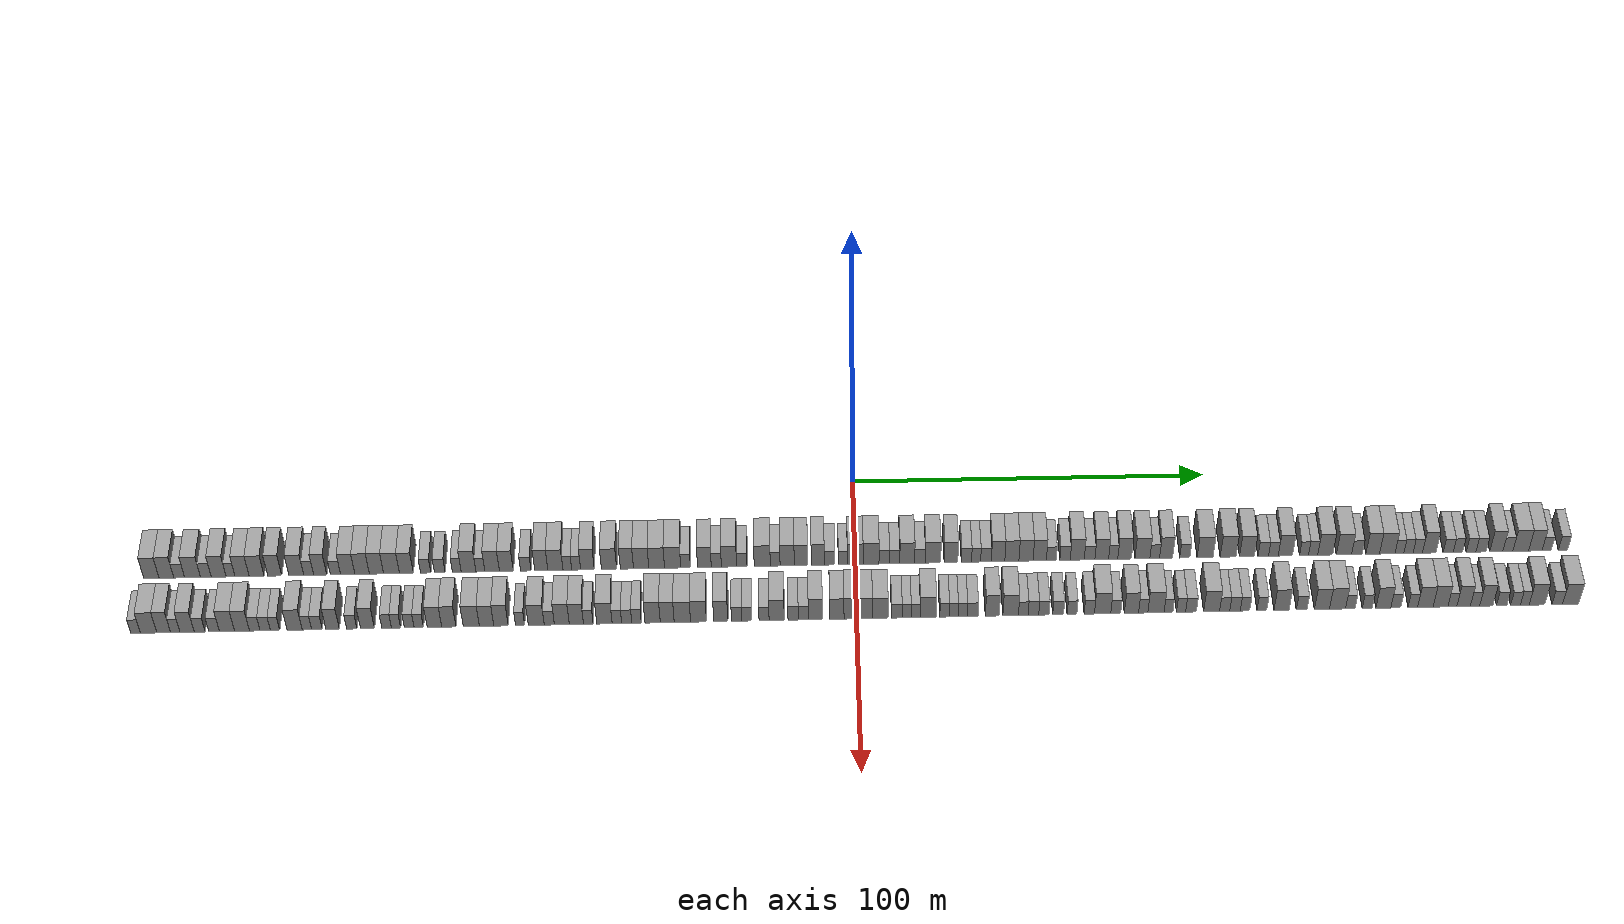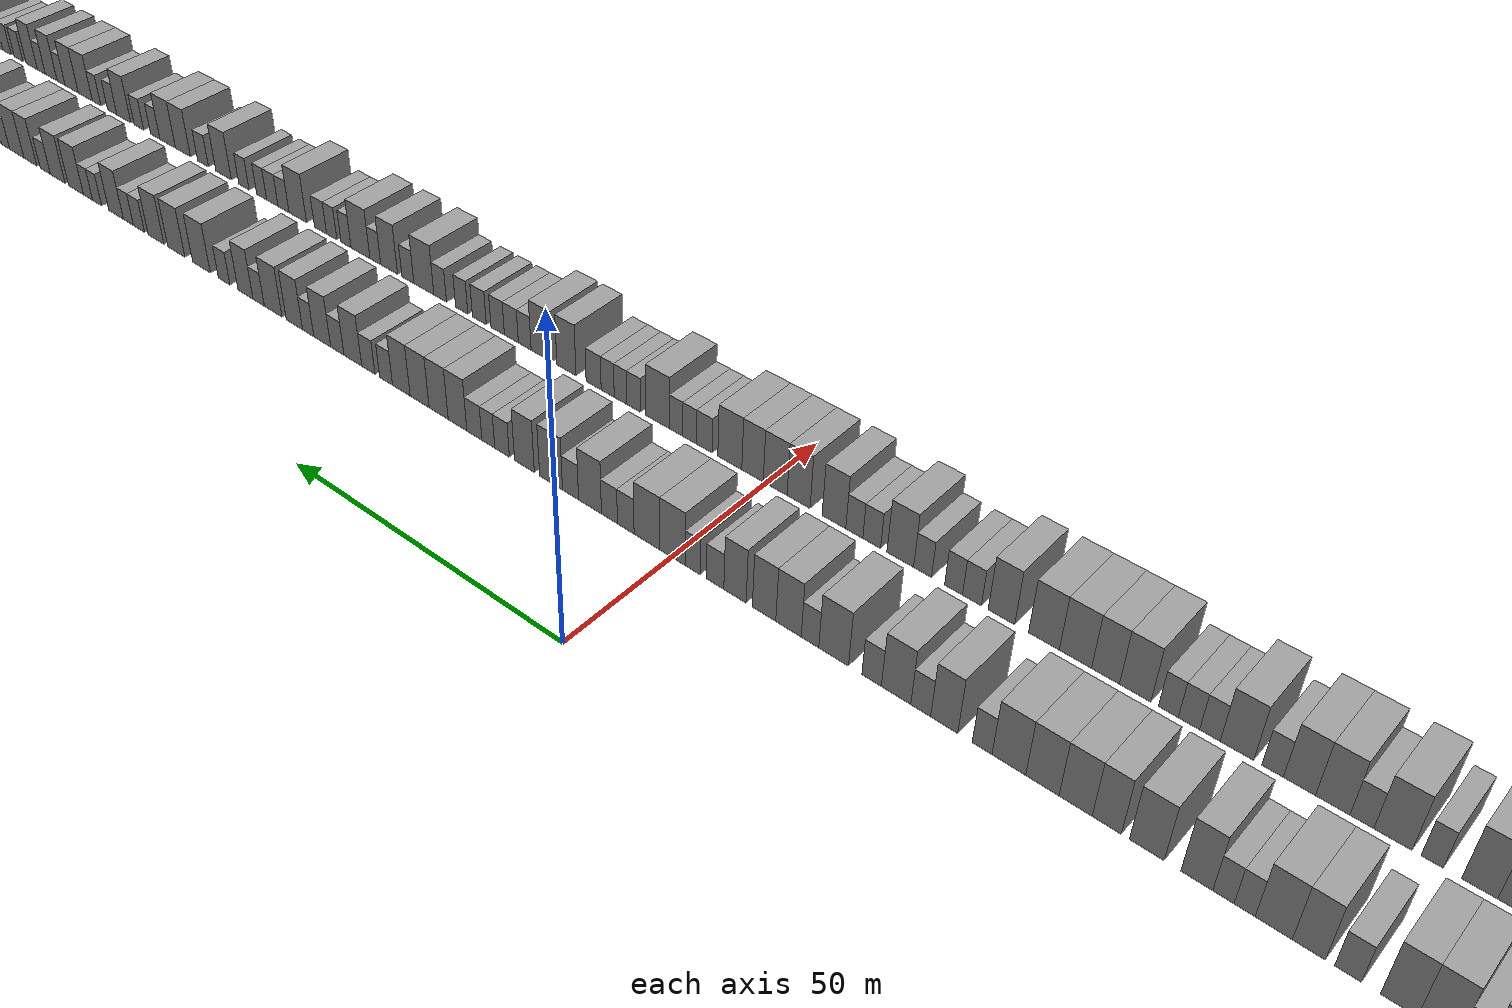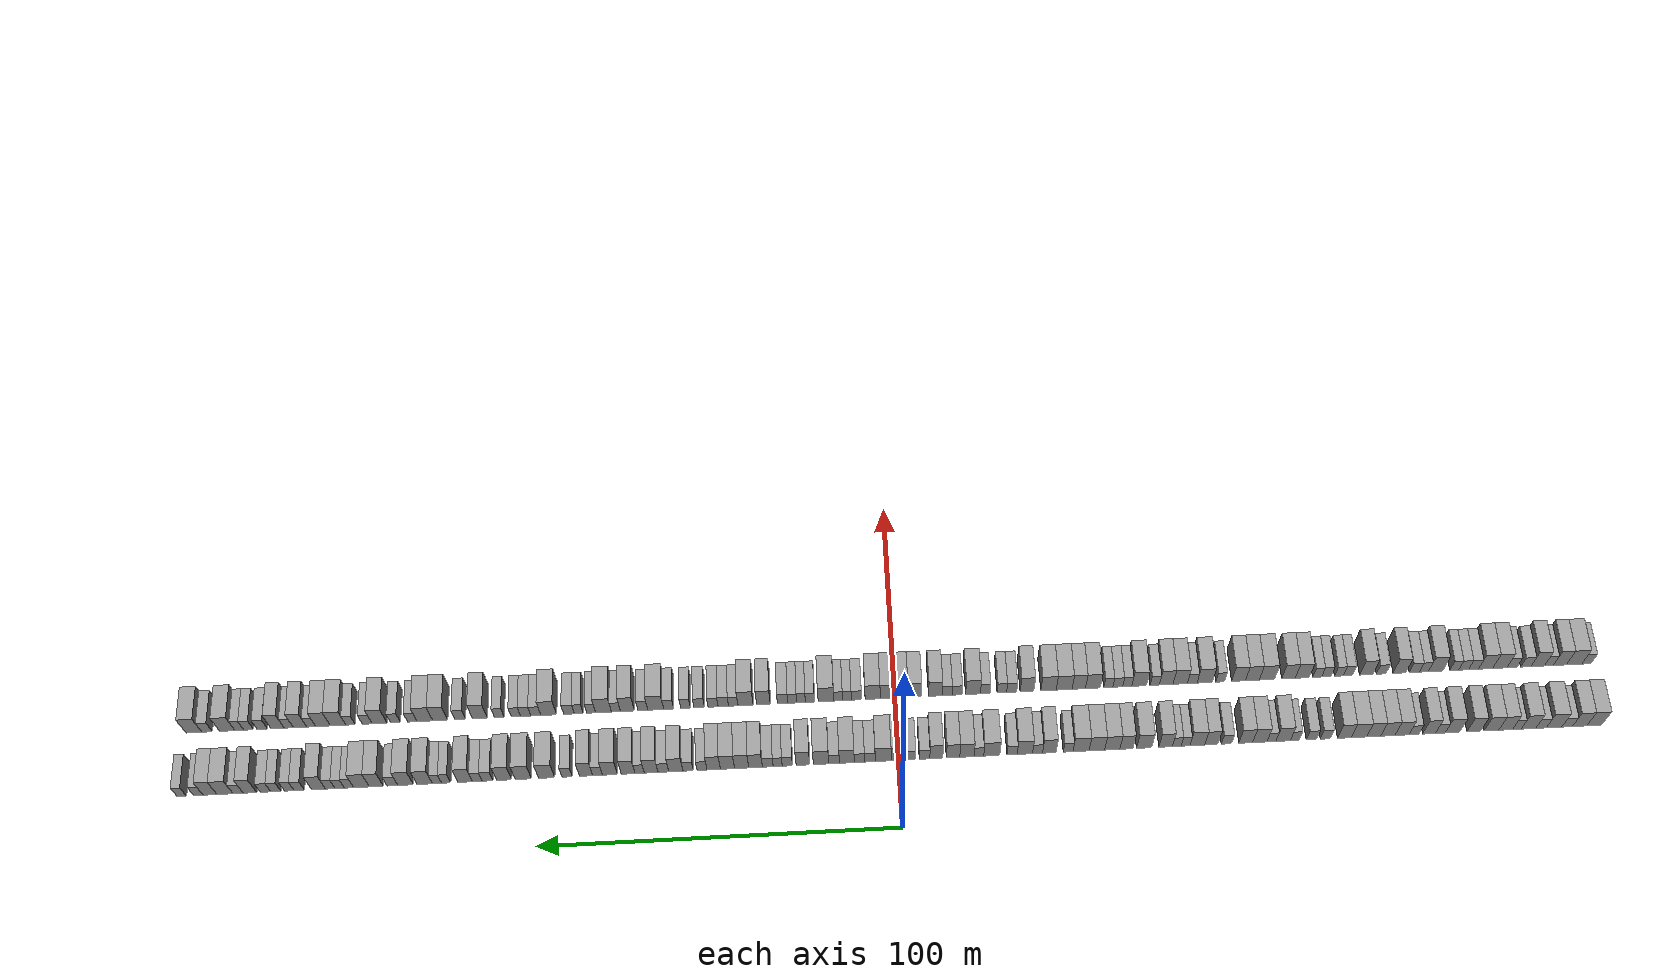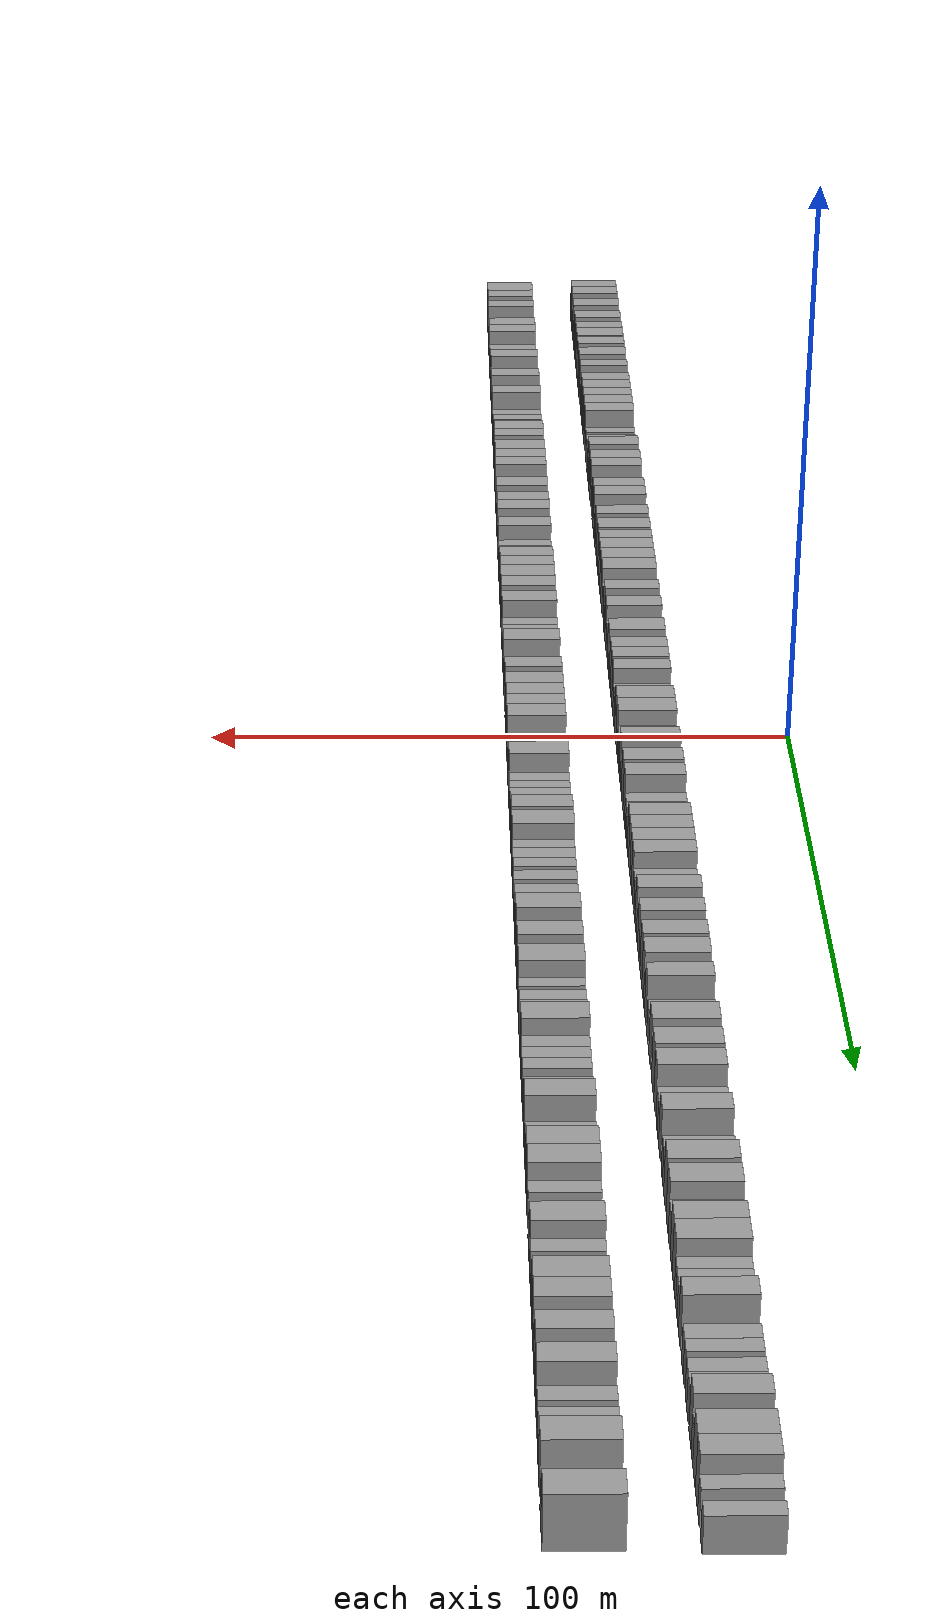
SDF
<sdf version="1.6">
 <world name="default">
  <scene>
   <sky><clouds><speed>12</speed></clouds></sky>
   <ambient>0.4 0.4 0.4 1</ambient>
   <background>0.7 0.7 0.7 1</background>
   <shadows>1</shadows>
  </scene>
  <gravity>0 0 -9.8066</gravity>
  <magnetic_field>6e-06 2.3e-05 -4.2e-05</magnetic_field>
  <physics default="0" name="default_physics" type="ode">
   <ode>
    <solver>
     <type>quick</type>
     <iters>10</iters>
     <sor>1.0</sor>
     <use_dynamic_moi_rescaling>0</use_dynamic_moi_rescaling>
    </solver>
    <constraints>
     <cfm>0</cfm>
     <erp>0.2</erp>
     <contact_max_correcting_vel>100</contact_max_correcting_vel>
     <contact_surface_layer>0.001</contact_surface_layer>
    </constraints>
   </ode>
   <max_step_size>0.004</max_step_size>
   <real_time_factor>1</real_time_factor>
   <real_time_update_rate>250</real_time_update_rate>
  </physics>
  <light name="sun" type="directional">
   <pose>0 0 10 0 0 0</pose>
   <diffuse>0.8 0.8 0.8 1</diffuse>
   <specular>0.2 0.2 0.2 1</specular>
   <attenuation>
    <range>1000</range>
    <constant>0.9</constant>
    <linear>0.01</linear>
    <quadratic>0.001</quadratic>
   </attenuation>
   <direction>-0.5 0.1 -0.9</direction>
  </light>
  <model name="building_1">
   <static>1</static>
   <pose>25.0000 -194.8984 0 0.000000 0.000000 0.000000</pose>
   <link name="link">
    <pose>0 0 4.50 0 0 0</pose>
    <collision name="collision"><geometry><box><size>10.0000 4.2031 9.0000</size></box></geometry></collision>
    <visual name="visual">
     <cast_shadows>0</cast_shadows>
     <geometry><box><size>10.0000 4.2031 9.0000</size></box></geometry>
     <material>
      <script>
       <uri>model://grey_wall/materials/scripts</uri>
       <uri>model://grey_wall/materials/textures</uri>
       <name>vrc/grey_wall</name>
      </script>
     </material>
    </visual>
   </link>
  </model>
  <model name="building_2">
   <static>1</static>
   <pose>25.0000 -190.7665 0 0.000000 0.000000 0.000000</pose>
   <link name="link">
    <pose>0 0 4.50 0 0 0</pose>
    <collision name="collision"><geometry><box><size>10.0000 4.0608 9.0000</size></box></geometry></collision>
    <visual name="visual">
     <cast_shadows>0</cast_shadows>
     <geometry><box><size>10.0000 4.0608 9.0000</size></box></geometry>
     <material>
      <script>
       <uri>model://grey_wall/materials/scripts</uri>
       <uri>model://grey_wall/materials/textures</uri>
       <name>vrc/grey_wall</name>
      </script>
     </material>
    </visual>
   </link>
  </model>
  <model name="building_3">
   <static>1</static>
   <pose>25.0000 -187.2383 0 0.000000 0.000000 0.000000</pose>
   <link name="link">
    <pose>0 0 3.00 0 0 0</pose>
    <collision name="collision"><geometry><box><size>10.0000 2.9955 6.0000</size></box></geometry></collision>
    <visual name="visual">
     <cast_shadows>0</cast_shadows>
     <geometry><box><size>10.0000 2.9955 6.0000</size></box></geometry>
     <material>
      <script>
       <uri>model://grey_wall/materials/scripts</uri>
       <uri>model://grey_wall/materials/textures</uri>
       <name>vrc/grey_wall</name>
      </script>
     </material>
    </visual>
   </link>
  </model>
  <model name="building_4">
   <static>1</static>
   <pose>25.0000 -183.5492 0 0.000000 0.000000 0.000000</pose>
   <link name="link">
    <pose>0 0 4.50 0 0 0</pose>
    <collision name="collision"><geometry><box><size>10.0000 4.3829 9.0000</size></box></geometry></collision>
    <visual name="visual">
     <cast_shadows>0</cast_shadows>
     <geometry><box><size>10.0000 4.3829 9.0000</size></box></geometry>
     <material>
      <script>
       <uri>model://grey_wall/materials/scripts</uri>
       <uri>model://grey_wall/materials/textures</uri>
       <name>vrc/grey_wall</name>
      </script>
     </material>
    </visual>
   </link>
  </model>
  <model name="building_5">
   <static>1</static>
   <pose>25.0000 -179.8770 0 0.000000 0.000000 0.000000</pose>
   <link name="link">
    <pose>0 0 3.00 0 0 0</pose>
    <collision name="collision"><geometry><box><size>10.0000 2.9615 6.0000</size></box></geometry></collision>
    <visual name="visual">
     <cast_shadows>0</cast_shadows>
     <geometry><box><size>10.0000 2.9615 6.0000</size></box></geometry>
     <material>
      <script>
       <uri>model://grey_wall/materials/scripts</uri>
       <uri>model://grey_wall/materials/textures</uri>
       <name>vrc/grey_wall</name>
      </script>
     </material>
    </visual>
   </link>
  </model>
  <model name="building_6">
   <static>1</static>
   <pose>25.0000 -176.3346 0 0.000000 0.000000 0.000000</pose>
   <link name="link">
    <pose>0 0 4.50 0 0 0</pose>
    <collision name="collision"><geometry><box><size>10.0000 4.1233 9.0000</size></box></geometry></collision>
    <visual name="visual">
     <cast_shadows>0</cast_shadows>
     <geometry><box><size>10.0000 4.1233 9.0000</size></box></geometry>
     <material>
      <script>
       <uri>model://grey_wall/materials/scripts</uri>
       <uri>model://grey_wall/materials/textures</uri>
       <name>vrc/grey_wall</name>
      </script>
     </material>
    </visual>
   </link>
  </model>
  <model name="building_7">
   <static>1</static>
   <pose>25.0000 -173.0549 0 0.000000 0.000000 0.000000</pose>
   <link name="link">
    <pose>0 0 3.00 0 0 0</pose>
    <collision name="collision"><geometry><box><size>10.0000 2.4361 6.0000</size></box></geometry></collision>
    <visual name="visual">
     <cast_shadows>0</cast_shadows>
     <geometry><box><size>10.0000 2.4361 6.0000</size></box></geometry>
     <material>
      <script>
       <uri>model://grey_wall/materials/scripts</uri>
       <uri>model://grey_wall/materials/textures</uri>
       <name>vrc/grey_wall</name>
      </script>
     </material>
    </visual>
   </link>
  </model>
  <model name="building_8">
   <static>1</static>
   <pose>25.0000 -169.8877 0 0.000000 0.000000 0.000000</pose>
   <link name="link">
    <pose>0 0 4.50 0 0 0</pose>
    <collision name="collision"><geometry><box><size>10.0000 3.8981 9.0000</size></box></geometry></collision>
    <visual name="visual">
     <cast_shadows>0</cast_shadows>
     <geometry><box><size>10.0000 3.8981 9.0000</size></box></geometry>
     <material>
      <script>
       <uri>model://grey_wall/materials/scripts</uri>
       <uri>model://grey_wall/materials/textures</uri>
       <name>vrc/grey_wall</name>
      </script>
     </material>
    </visual>
   </link>
  </model>
  <model name="building_9">
   <static>1</static>
   <pose>25.0000 -165.8667 0 0.000000 0.000000 0.000000</pose>
   <link name="link">
    <pose>0 0 4.50 0 0 0</pose>
    <collision name="collision"><geometry><box><size>10.0000 4.1438 9.0000</size></box></geometry></collision>
    <visual name="visual">
     <cast_shadows>0</cast_shadows>
     <geometry><box><size>10.0000 4.1438 9.0000</size></box></geometry>
     <material>
      <script>
       <uri>model://grey_wall/materials/scripts</uri>
       <uri>model://grey_wall/materials/textures</uri>
       <name>vrc/grey_wall</name>
      </script>
     </material>
    </visual>
   </link>
  </model>
  <model name="building_10">
   <static>1</static>
   <pose>25.0000 -160.8722 0 0.000000 0.000000 0.000000</pose>
   <link name="link">
    <pose>0 0 4.50 0 0 0</pose>
    <collision name="collision"><geometry><box><size>10.0000 3.8452 9.0000</size></box></geometry></collision>
    <visual name="visual">
     <cast_shadows>0</cast_shadows>
     <geometry><box><size>10.0000 3.8452 9.0000</size></box></geometry>
     <material>
      <script>
       <uri>model://grey_wall/materials/scripts</uri>
       <uri>model://grey_wall/materials/textures</uri>
       <name>vrc/grey_wall</name>
      </script>
     </material>
    </visual>
   </link>
  </model>
  <model name="building_11">
   <static>1</static>
   <pose>25.0000 -154.9100 0 0.000000 0.000000 0.000000</pose>
   <link name="link">
    <pose>0 0 4.50 0 0 0</pose>
    <collision name="collision"><geometry><box><size>10.0000 4.0792 9.0000</size></box></geometry></collision>
    <visual name="visual">
     <cast_shadows>0</cast_shadows>
     <geometry><box><size>10.0000 4.0792 9.0000</size></box></geometry>
     <material>
      <script>
       <uri>model://grey_wall/materials/scripts</uri>
       <uri>model://grey_wall/materials/textures</uri>
       <name>vrc/grey_wall</name>
      </script>
     </material>
    </visual>
   </link>
  </model>
  <model name="building_12">
   <static>1</static>
   <pose>25.0000 -151.4968 0 0.000000 0.000000 0.000000</pose>
   <link name="link">
    <pose>0 0 3.00 0 0 0</pose>
    <collision name="collision"><geometry><box><size>10.0000 2.7471 6.0000</size></box></geometry></collision>
    <visual name="visual">
     <cast_shadows>0</cast_shadows>
     <geometry><box><size>10.0000 2.7471 6.0000</size></box></geometry>
     <material>
      <script>
       <uri>model://grey_wall/materials/scripts</uri>
       <uri>model://grey_wall/materials/textures</uri>
       <name>vrc/grey_wall</name>
      </script>
     </material>
    </visual>
   </link>
  </model>
  <model name="building_13">
   <static>1</static>
   <pose>25.0000 -148.3091 0 0.000000 0.000000 0.000000</pose>
   <link name="link">
    <pose>0 0 4.50 0 0 0</pose>
    <collision name="collision"><geometry><box><size>10.0000 3.6283 9.0000</size></box></geometry></collision>
    <visual name="visual">
     <cast_shadows>0</cast_shadows>
     <geometry><box><size>10.0000 3.6283 9.0000</size></box></geometry>
     <material>
      <script>
       <uri>model://grey_wall/materials/scripts</uri>
       <uri>model://grey_wall/materials/textures</uri>
       <name>vrc/grey_wall</name>
      </script>
     </material>
    </visual>
   </link>
  </model>
  <model name="building_14">
   <static>1</static>
   <pose>25.0000 -144.0852 0 0.000000 0.000000 0.000000</pose>
   <link name="link">
    <pose>0 0 3.00 0 0 0</pose>
    <collision name="collision"><geometry><box><size>10.0000 2.8194 6.0000</size></box></geometry></collision>
    <visual name="visual">
     <cast_shadows>0</cast_shadows>
     <geometry><box><size>10.0000 2.8194 6.0000</size></box></geometry>
     <material>
      <script>
       <uri>model://grey_wall/materials/scripts</uri>
       <uri>model://grey_wall/materials/textures</uri>
       <name>vrc/grey_wall</name>
      </script>
     </material>
    </visual>
   </link>
  </model>
  <model name="building_15">
   <static>1</static>
   <pose>25.0000 -140.6982 0 0.000000 0.000000 0.000000</pose>
   <link name="link">
    <pose>0 0 4.50 0 0 0</pose>
    <collision name="collision"><geometry><box><size>10.0000 3.9545 9.0000</size></box></geometry></collision>
    <visual name="visual">
     <cast_shadows>0</cast_shadows>
     <geometry><box><size>10.0000 3.9545 9.0000</size></box></geometry>
     <material>
      <script>
       <uri>model://grey_wall/materials/scripts</uri>
       <uri>model://grey_wall/materials/textures</uri>
       <name>vrc/grey_wall</name>
      </script>
     </material>
    </visual>
   </link>
  </model>
  <model name="building_16">
   <static>1</static>
   <pose>25.0000 -136.7213 0 0.000000 0.000000 0.000000</pose>
   <link name="link">
    <pose>0 0 4.50 0 0 0</pose>
    <collision name="collision"><geometry><box><size>10.0000 3.9994 9.0000</size></box></geometry></collision>
    <visual name="visual">
     <cast_shadows>0</cast_shadows>
     <geometry><box><size>10.0000 3.9994 9.0000</size></box></geometry>
     <material>
      <script>
       <uri>model://grey_wall/materials/scripts</uri>
       <uri>model://grey_wall/materials/textures</uri>
       <name>vrc/grey_wall</name>
      </script>
     </material>
    </visual>
   </link>
  </model>
  <model name="building_17">
   <static>1</static>
   <pose>25.0000 -132.7497 0 0.000000 0.000000 0.000000</pose>
   <link name="link">
    <pose>0 0 4.50 0 0 0</pose>
    <collision name="collision"><geometry><box><size>10.0000 3.9437 9.0000</size></box></geometry></collision>
    <visual name="visual">
     <cast_shadows>0</cast_shadows>
     <geometry><box><size>10.0000 3.9437 9.0000</size></box></geometry>
     <material>
      <script>
       <uri>model://grey_wall/materials/scripts</uri>
       <uri>model://grey_wall/materials/textures</uri>
       <name>vrc/grey_wall</name>
      </script>
     </material>
    </visual>
   </link>
  </model>
  <model name="building_18">
   <static>1</static>
   <pose>25.0000 -128.5824 0 0.000000 0.000000 0.000000</pose>
   <link name="link">
    <pose>0 0 4.50 0 0 0</pose>
    <collision name="collision"><geometry><box><size>10.0000 4.3910 9.0000</size></box></geometry></collision>
    <visual name="visual">
     <cast_shadows>0</cast_shadows>
     <geometry><box><size>10.0000 4.3910 9.0000</size></box></geometry>
     <material>
      <script>
       <uri>model://grey_wall/materials/scripts</uri>
       <uri>model://grey_wall/materials/textures</uri>
       <name>vrc/grey_wall</name>
      </script>
     </material>
    </visual>
   </link>
  </model>
  <model name="building_19">
   <static>1</static>
   <pose>25.0000 -124.4751 0 0.000000 0.000000 0.000000</pose>
   <link name="link">
    <pose>0 0 4.50 0 0 0</pose>
    <collision name="collision"><geometry><box><size>10.0000 3.8236 9.0000</size></box></geometry></collision>
    <visual name="visual">
     <cast_shadows>0</cast_shadows>
     <geometry><box><size>10.0000 3.8236 9.0000</size></box></geometry>
     <material>
      <script>
       <uri>model://grey_wall/materials/scripts</uri>
       <uri>model://grey_wall/materials/textures</uri>
       <name>vrc/grey_wall</name>
      </script>
     </material>
    </visual>
   </link>
  </model>
  <model name="building_20">
   <static>1</static>
   <pose>25.0000 -119.1442 0 0.000000 0.000000 0.000000</pose>
   <link name="link">
    <pose>0 0 3.00 0 0 0</pose>
    <collision name="collision"><geometry><box><size>10.0000 2.8384 6.0000</size></box></geometry></collision>
    <visual name="visual">
     <cast_shadows>0</cast_shadows>
     <geometry><box><size>10.0000 2.8384 6.0000</size></box></geometry>
     <material>
      <script>
       <uri>model://grey_wall/materials/scripts</uri>
       <uri>model://grey_wall/materials/textures</uri>
       <name>vrc/grey_wall</name>
      </script>
     </material>
    </visual>
   </link>
  </model>
  <model name="building_21">
   <static>1</static>
   <pose>25.0000 -115.2415 0 0.000000 0.000000 0.000000</pose>
   <link name="link">
    <pose>0 0 3.00 0 0 0</pose>
    <collision name="collision"><geometry><box><size>10.0000 2.9668 6.0000</size></box></geometry></collision>
    <visual name="visual">
     <cast_shadows>0</cast_shadows>
     <geometry><box><size>10.0000 2.9668 6.0000</size></box></geometry>
     <material>
      <script>
       <uri>model://grey_wall/materials/scripts</uri>
       <uri>model://grey_wall/materials/textures</uri>
       <name>vrc/grey_wall</name>
      </script>
     </material>
    </visual>
   </link>
  </model>
  <model name="building_22">
   <static>1</static>
   <pose>25.0000 -110.5352 0 0.000000 0.000000 0.000000</pose>
   <link name="link">
    <pose>0 0 3.00 0 0 0</pose>
    <collision name="collision"><geometry><box><size>10.0000 2.4459 6.0000</size></box></geometry></collision>
    <visual name="visual">
     <cast_shadows>0</cast_shadows>
     <geometry><box><size>10.0000 2.4459 6.0000</size></box></geometry>
     <material>
      <script>
       <uri>model://grey_wall/materials/scripts</uri>
       <uri>model://grey_wall/materials/textures</uri>
       <name>vrc/grey_wall</name>
      </script>
     </material>
    </visual>
   </link>
  </model>
  <model name="building_23">
   <static>1</static>
   <pose>25.0000 -107.2818 0 0.000000 0.000000 0.000000</pose>
   <link name="link">
    <pose>0 0 4.50 0 0 0</pose>
    <collision name="collision"><geometry><box><size>10.0000 4.0610 9.0000</size></box></geometry></collision>
    <visual name="visual">
     <cast_shadows>0</cast_shadows>
     <geometry><box><size>10.0000 4.0610 9.0000</size></box></geometry>
     <material>
      <script>
       <uri>model://grey_wall/materials/scripts</uri>
       <uri>model://grey_wall/materials/textures</uri>
       <name>vrc/grey_wall</name>
      </script>
     </material>
    </visual>
   </link>
  </model>
  <model name="building_24">
   <static>1</static>
   <pose>25.0000 -104.0030 0 0.000000 0.000000 0.000000</pose>
   <link name="link">
    <pose>0 0 3.00 0 0 0</pose>
    <collision name="collision"><geometry><box><size>10.0000 2.4966 6.0000</size></box></geometry></collision>
    <visual name="visual">
     <cast_shadows>0</cast_shadows>
     <geometry><box><size>10.0000 2.4966 6.0000</size></box></geometry>
     <material>
      <script>
       <uri>model://grey_wall/materials/scripts</uri>
       <uri>model://grey_wall/materials/textures</uri>
       <name>vrc/grey_wall</name>
      </script>
     </material>
    </visual>
   </link>
  </model>
  <model name="building_25">
   <static>1</static>
   <pose>25.0000 -100.7431 0 0.000000 0.000000 0.000000</pose>
   <link name="link">
    <pose>0 0 4.50 0 0 0</pose>
    <collision name="collision"><geometry><box><size>10.0000 4.0231 9.0000</size></box></geometry></collision>
    <visual name="visual">
     <cast_shadows>0</cast_shadows>
     <geometry><box><size>10.0000 4.0231 9.0000</size></box></geometry>
     <material>
      <script>
       <uri>model://grey_wall/materials/scripts</uri>
       <uri>model://grey_wall/materials/textures</uri>
       <name>vrc/grey_wall</name>
      </script>
     </material>
    </visual>
   </link>
  </model>
  <model name="building_26">
   <static>1</static>
   <pose>25.0000 -96.7978 0 0.000000 0.000000 0.000000</pose>
   <link name="link">
    <pose>0 0 4.50 0 0 0</pose>
    <collision name="collision"><geometry><box><size>10.0000 3.8676 9.0000</size></box></geometry></collision>
    <visual name="visual">
     <cast_shadows>0</cast_shadows>
     <geometry><box><size>10.0000 3.8676 9.0000</size></box></geometry>
     <material>
      <script>
       <uri>model://grey_wall/materials/scripts</uri>
       <uri>model://grey_wall/materials/textures</uri>
       <name>vrc/grey_wall</name>
      </script>
     </material>
    </visual>
   </link>
  </model>
  <model name="building_27">
   <static>1</static>
   <pose>25.0000 -91.4139 0 0.000000 0.000000 0.000000</pose>
   <link name="link">
    <pose>0 0 3.00 0 0 0</pose>
    <collision name="collision"><geometry><box><size>10.0000 2.9003 6.0000</size></box></geometry></collision>
    <visual name="visual">
     <cast_shadows>0</cast_shadows>
     <geometry><box><size>10.0000 2.9003 6.0000</size></box></geometry>
     <material>
      <script>
       <uri>model://grey_wall/materials/scripts</uri>
       <uri>model://grey_wall/materials/textures</uri>
       <name>vrc/grey_wall</name>
      </script>
     </material>
    </visual>
   </link>
  </model>
  <model name="building_28">
   <static>1</static>
   <pose>25.0000 -87.1407 0 0.000000 0.000000 0.000000</pose>
   <link name="link">
    <pose>0 0 4.50 0 0 0</pose>
    <collision name="collision"><geometry><box><size>10.0000 3.6459 9.0000</size></box></geometry></collision>
    <visual name="visual">
     <cast_shadows>0</cast_shadows>
     <geometry><box><size>10.0000 3.6459 9.0000</size></box></geometry>
     <material>
      <script>
       <uri>model://grey_wall/materials/scripts</uri>
       <uri>model://grey_wall/materials/textures</uri>
       <name>vrc/grey_wall</name>
      </script>
     </material>
    </visual>
   </link>
  </model>
  <model name="building_29">
   <static>1</static>
   <pose>25.0000 -83.2249 0 0.000000 0.000000 0.000000</pose>
   <link name="link">
    <pose>0 0 4.50 0 0 0</pose>
    <collision name="collision"><geometry><box><size>10.0000 4.1856 9.0000</size></box></geometry></collision>
    <visual name="visual">
     <cast_shadows>0</cast_shadows>
     <geometry><box><size>10.0000 4.1856 9.0000</size></box></geometry>
     <material>
      <script>
       <uri>model://grey_wall/materials/scripts</uri>
       <uri>model://grey_wall/materials/textures</uri>
       <name>vrc/grey_wall</name>
      </script>
     </material>
    </visual>
   </link>
  </model>
  <model name="building_30">
   <static>1</static>
   <pose>25.0000 -79.9210 0 0.000000 0.000000 0.000000</pose>
   <link name="link">
    <pose>0 0 3.00 0 0 0</pose>
    <collision name="collision"><geometry><box><size>10.0000 2.4223 6.0000</size></box></geometry></collision>
    <visual name="visual">
     <cast_shadows>0</cast_shadows>
     <geometry><box><size>10.0000 2.4223 6.0000</size></box></geometry>
     <material>
      <script>
       <uri>model://grey_wall/materials/scripts</uri>
       <uri>model://grey_wall/materials/textures</uri>
       <name>vrc/grey_wall</name>
      </script>
     </material>
    </visual>
   </link>
  </model>
  <model name="building_31">
   <static>1</static>
   <pose>25.0000 -77.4762 0 0.000000 0.000000 0.000000</pose>
   <link name="link">
    <pose>0 0 3.00 0 0 0</pose>
    <collision name="collision"><geometry><box><size>10.0000 2.4674 6.0000</size></box></geometry></collision>
    <visual name="visual">
     <cast_shadows>0</cast_shadows>
     <geometry><box><size>10.0000 2.4674 6.0000</size></box></geometry>
     <material>
      <script>
       <uri>model://grey_wall/materials/scripts</uri>
       <uri>model://grey_wall/materials/textures</uri>
       <name>vrc/grey_wall</name>
      </script>
     </material>
    </visual>
   </link>
  </model>
  <model name="building_32">
   <static>1</static>
   <pose>25.0000 -74.3567 0 0.000000 0.000000 0.000000</pose>
   <link name="link">
    <pose>0 0 4.50 0 0 0</pose>
    <collision name="collision"><geometry><box><size>10.0000 3.7716 9.0000</size></box></geometry></collision>
    <visual name="visual">
     <cast_shadows>0</cast_shadows>
     <geometry><box><size>10.0000 3.7716 9.0000</size></box></geometry>
     <material>
      <script>
       <uri>model://grey_wall/materials/scripts</uri>
       <uri>model://grey_wall/materials/textures</uri>
       <name>vrc/grey_wall</name>
      </script>
     </material>
    </visual>
   </link>
  </model>
  <model name="building_33">
   <static>1</static>
   <pose>25.0000 -68.3508 0 0.000000 0.000000 0.000000</pose>
   <link name="link">
    <pose>0 0 4.50 0 0 0</pose>
    <collision name="collision"><geometry><box><size>10.0000 4.2402 9.0000</size></box></geometry></collision>
    <visual name="visual">
     <cast_shadows>0</cast_shadows>
     <geometry><box><size>10.0000 4.2402 9.0000</size></box></geometry>
     <material>
      <script>
       <uri>model://grey_wall/materials/scripts</uri>
       <uri>model://grey_wall/materials/textures</uri>
       <name>vrc/grey_wall</name>
      </script>
     </material>
    </visual>
   </link>
  </model>
  <model name="building_34">
   <static>1</static>
   <pose>25.0000 -63.4051 0 0.000000 0.000000 0.000000</pose>
   <link name="link">
    <pose>0 0 4.50 0 0 0</pose>
    <collision name="collision"><geometry><box><size>10.0000 3.6512 9.0000</size></box></geometry></collision>
    <visual name="visual">
     <cast_shadows>0</cast_shadows>
     <geometry><box><size>10.0000 3.6512 9.0000</size></box></geometry>
     <material>
      <script>
       <uri>model://grey_wall/materials/scripts</uri>
       <uri>model://grey_wall/materials/textures</uri>
       <name>vrc/grey_wall</name>
      </script>
     </material>
    </visual>
   </link>
  </model>
  <model name="building_35">
   <static>1</static>
   <pose>25.0000 -59.4551 0 0.000000 0.000000 0.000000</pose>
   <link name="link">
    <pose>0 0 4.50 0 0 0</pose>
    <collision name="collision"><geometry><box><size>10.0000 4.2489 9.0000</size></box></geometry></collision>
    <visual name="visual">
     <cast_shadows>0</cast_shadows>
     <geometry><box><size>10.0000 4.2489 9.0000</size></box></geometry>
     <material>
      <script>
       <uri>model://grey_wall/materials/scripts</uri>
       <uri>model://grey_wall/materials/textures</uri>
       <name>vrc/grey_wall</name>
      </script>
     </material>
    </visual>
   </link>
  </model>
  <model name="building_36">
   <static>1</static>
   <pose>25.0000 -55.1491 0 0.000000 0.000000 0.000000</pose>
   <link name="link">
    <pose>0 0 4.50 0 0 0</pose>
    <collision name="collision"><geometry><box><size>10.0000 4.3631 9.0000</size></box></geometry></collision>
    <visual name="visual">
     <cast_shadows>0</cast_shadows>
     <geometry><box><size>10.0000 4.3631 9.0000</size></box></geometry>
     <material>
      <script>
       <uri>model://grey_wall/materials/scripts</uri>
       <uri>model://grey_wall/materials/textures</uri>
       <name>vrc/grey_wall</name>
      </script>
     </material>
    </visual>
   </link>
  </model>
  <model name="building_37">
   <static>1</static>
   <pose>25.0000 -50.7211 0 0.000000 0.000000 0.000000</pose>
   <link name="link">
    <pose>0 0 4.50 0 0 0</pose>
    <collision name="collision"><geometry><box><size>10.0000 4.4929 9.0000</size></box></geometry></collision>
    <visual name="visual">
     <cast_shadows>0</cast_shadows>
     <geometry><box><size>10.0000 4.4929 9.0000</size></box></geometry>
     <material>
      <script>
       <uri>model://grey_wall/materials/scripts</uri>
       <uri>model://grey_wall/materials/textures</uri>
       <name>vrc/grey_wall</name>
      </script>
     </material>
    </visual>
   </link>
  </model>
  <model name="building_38">
   <static>1</static>
   <pose>25.0000 -47.1336 0 0.000000 0.000000 0.000000</pose>
   <link name="link">
    <pose>0 0 3.00 0 0 0</pose>
    <collision name="collision"><geometry><box><size>10.0000 2.6821 6.0000</size></box></geometry></collision>
    <visual name="visual">
     <cast_shadows>0</cast_shadows>
     <geometry><box><size>10.0000 2.6821 6.0000</size></box></geometry>
     <material>
      <script>
       <uri>model://grey_wall/materials/scripts</uri>
       <uri>model://grey_wall/materials/textures</uri>
       <name>vrc/grey_wall</name>
      </script>
     </material>
    </visual>
   </link>
  </model>
  <model name="building_39">
   <static>1</static>
   <pose>25.0000 -41.9003 0 0.000000 0.000000 0.000000</pose>
   <link name="link">
    <pose>0 0 4.50 0 0 0</pose>
    <collision name="collision"><geometry><box><size>10.0000 3.7845 9.0000</size></box></geometry></collision>
    <visual name="visual">
     <cast_shadows>0</cast_shadows>
     <geometry><box><size>10.0000 3.7845 9.0000</size></box></geometry>
     <material>
      <script>
       <uri>model://grey_wall/materials/scripts</uri>
       <uri>model://grey_wall/materials/textures</uri>
       <name>vrc/grey_wall</name>
      </script>
     </material>
    </visual>
   </link>
  </model>
  <model name="building_40">
   <static>1</static>
   <pose>25.0000 -38.6015 0 0.000000 0.000000 0.000000</pose>
   <link name="link">
    <pose>0 0 3.00 0 0 0</pose>
    <collision name="collision"><geometry><box><size>10.0000 2.8131 6.0000</size></box></geometry></collision>
    <visual name="visual">
     <cast_shadows>0</cast_shadows>
     <geometry><box><size>10.0000 2.8131 6.0000</size></box></geometry>
     <material>
      <script>
       <uri>model://grey_wall/materials/scripts</uri>
       <uri>model://grey_wall/materials/textures</uri>
       <name>vrc/grey_wall</name>
      </script>
     </material>
    </visual>
   </link>
  </model>
  <model name="building_41">
   <static>1</static>
   <pose>25.0000 -35.0680 0 0.000000 0.000000 0.000000</pose>
   <link name="link">
    <pose>0 0 4.50 0 0 0</pose>
    <collision name="collision"><geometry><box><size>10.0000 4.2538 9.0000</size></box></geometry></collision>
    <visual name="visual">
     <cast_shadows>0</cast_shadows>
     <geometry><box><size>10.0000 4.2538 9.0000</size></box></geometry>
     <material>
      <script>
       <uri>model://grey_wall/materials/scripts</uri>
       <uri>model://grey_wall/materials/textures</uri>
       <name>vrc/grey_wall</name>
      </script>
     </material>
    </visual>
   </link>
  </model>
  <model name="building_42">
   <static>1</static>
   <pose>25.0000 -31.5135 0 0.000000 0.000000 0.000000</pose>
   <link name="link">
    <pose>0 0 3.00 0 0 0</pose>
    <collision name="collision"><geometry><box><size>10.0000 2.8553 6.0000</size></box></geometry></collision>
    <visual name="visual">
     <cast_shadows>0</cast_shadows>
     <geometry><box><size>10.0000 2.8553 6.0000</size></box></geometry>
     <material>
      <script>
       <uri>model://grey_wall/materials/scripts</uri>
       <uri>model://grey_wall/materials/textures</uri>
       <name>vrc/grey_wall</name>
      </script>
     </material>
    </visual>
   </link>
  </model>
  <model name="building_43">
   <static>1</static>
   <pose>25.0000 -25.8438 0 0.000000 0.000000 0.000000</pose>
   <link name="link">
    <pose>0 0 4.50 0 0 0</pose>
    <collision name="collision"><geometry><box><size>10.0000 4.4839 9.0000</size></box></geometry></collision>
    <visual name="visual">
     <cast_shadows>0</cast_shadows>
     <geometry><box><size>10.0000 4.4839 9.0000</size></box></geometry>
     <material>
      <script>
       <uri>model://grey_wall/materials/scripts</uri>
       <uri>model://grey_wall/materials/textures</uri>
       <name>vrc/grey_wall</name>
      </script>
     </material>
    </visual>
   </link>
  </model>
  <model name="building_44">
   <static>1</static>
   <pose>25.0000 -22.2543 0 0.000000 0.000000 0.000000</pose>
   <link name="link">
    <pose>0 0 3.00 0 0 0</pose>
    <collision name="collision"><geometry><box><size>10.0000 2.6952 6.0000</size></box></geometry></collision>
    <visual name="visual">
     <cast_shadows>0</cast_shadows>
     <geometry><box><size>10.0000 2.6952 6.0000</size></box></geometry>
     <material>
      <script>
       <uri>model://grey_wall/materials/scripts</uri>
       <uri>model://grey_wall/materials/textures</uri>
       <name>vrc/grey_wall</name>
      </script>
     </material>
    </visual>
   </link>
  </model>
  <model name="building_45">
   <static>1</static>
   <pose>25.0000 -18.9246 0 0.000000 0.000000 0.000000</pose>
   <link name="link">
    <pose>0 0 4.50 0 0 0</pose>
    <collision name="collision"><geometry><box><size>10.0000 3.9641 9.0000</size></box></geometry></collision>
    <visual name="visual">
     <cast_shadows>0</cast_shadows>
     <geometry><box><size>10.0000 3.9641 9.0000</size></box></geometry>
     <material>
      <script>
       <uri>model://grey_wall/materials/scripts</uri>
       <uri>model://grey_wall/materials/textures</uri>
       <name>vrc/grey_wall</name>
      </script>
     </material>
    </visual>
   </link>
  </model>
  <model name="building_46">
   <static>1</static>
   <pose>25.0000 -15.0828 0 0.000000 0.000000 0.000000</pose>
   <link name="link">
    <pose>0 0 4.50 0 0 0</pose>
    <collision name="collision"><geometry><box><size>10.0000 3.7196 9.0000</size></box></geometry></collision>
    <visual name="visual">
     <cast_shadows>0</cast_shadows>
     <geometry><box><size>10.0000 3.7196 9.0000</size></box></geometry>
     <material>
      <script>
       <uri>model://grey_wall/materials/scripts</uri>
       <uri>model://grey_wall/materials/textures</uri>
       <name>vrc/grey_wall</name>
      </script>
     </material>
    </visual>
   </link>
  </model>
  <model name="building_47">
   <static>1</static>
   <pose>25.0000 -10.4164 0 0.000000 0.000000 0.000000</pose>
   <link name="link">
    <pose>0 0 4.50 0 0 0</pose>
    <collision name="collision"><geometry><box><size>10.0000 3.6133 9.0000</size></box></geometry></collision>
    <visual name="visual">
     <cast_shadows>0</cast_shadows>
     <geometry><box><size>10.0000 3.6133 9.0000</size></box></geometry>
     <material>
      <script>
       <uri>model://grey_wall/materials/scripts</uri>
       <uri>model://grey_wall/materials/textures</uri>
       <name>vrc/grey_wall</name>
      </script>
     </material>
    </visual>
   </link>
  </model>
  <model name="building_48">
   <static>1</static>
   <pose>25.0000 -7.1538 0 0.000000 0.000000 0.000000</pose>
   <link name="link">
    <pose>0 0 3.00 0 0 0</pose>
    <collision name="collision"><geometry><box><size>10.0000 2.9118 6.0000</size></box></geometry></collision>
    <visual name="visual">
     <cast_shadows>0</cast_shadows>
     <geometry><box><size>10.0000 2.9118 6.0000</size></box></geometry>
     <material>
      <script>
       <uri>model://grey_wall/materials/scripts</uri>
       <uri>model://grey_wall/materials/textures</uri>
       <name>vrc/grey_wall</name>
      </script>
     </material>
    </visual>
   </link>
  </model>
  <model name="building_49">
   <static>1</static>
   <pose>25.0000 -3.4486 0 0.000000 0.000000 0.000000</pose>
   <link name="link">
    <pose>0 0 3.00 0 0 0</pose>
    <collision name="collision"><geometry><box><size>10.0000 2.4985 6.0000</size></box></geometry></collision>
    <visual name="visual">
     <cast_shadows>0</cast_shadows>
     <geometry><box><size>10.0000 2.4985 6.0000</size></box></geometry>
     <material>
      <script>
       <uri>model://grey_wall/materials/scripts</uri>
       <uri>model://grey_wall/materials/textures</uri>
       <name>vrc/grey_wall</name>
      </script>
     </material>
    </visual>
   </link>
  </model>
  <model name="building_50">
   <static>1</static>
   <pose>25.0000 -0.0272 0 0.000000 0.000000 0.000000</pose>
   <link name="link">
    <pose>0 0 4.50 0 0 0</pose>
    <collision name="collision"><geometry><box><size>10.0000 4.3445 9.0000</size></box></geometry></collision>
    <visual name="visual">
     <cast_shadows>0</cast_shadows>
     <geometry><box><size>10.0000 4.3445 9.0000</size></box></geometry>
     <material>
      <script>
       <uri>model://grey_wall/materials/scripts</uri>
       <uri>model://grey_wall/materials/textures</uri>
       <name>vrc/grey_wall</name>
      </script>
     </material>
    </visual>
   </link>
  </model>
  <model name="building_51">
   <static>1</static>
   <pose>25.0000 4.3547 0 0.000000 0.000000 0.000000</pose>
   <link name="link">
    <pose>0 0 4.50 0 0 0</pose>
    <collision name="collision"><geometry><box><size>10.0000 4.4192 9.0000</size></box></geometry></collision>
    <visual name="visual">
     <cast_shadows>0</cast_shadows>
     <geometry><box><size>10.0000 4.4192 9.0000</size></box></geometry>
     <material>
      <script>
       <uri>model://grey_wall/materials/scripts</uri>
       <uri>model://grey_wall/materials/textures</uri>
       <name>vrc/grey_wall</name>
      </script>
     </material>
    </visual>
   </link>
  </model>
  <model name="building_52">
   <static>1</static>
   <pose>25.0000 8.0335 0 0.000000 0.000000 0.000000</pose>
   <link name="link">
    <pose>0 0 3.00 0 0 0</pose>
    <collision name="collision"><geometry><box><size>10.0000 2.9385 6.0000</size></box></geometry></collision>
    <visual name="visual">
     <cast_shadows>0</cast_shadows>
     <geometry><box><size>10.0000 2.9385 6.0000</size></box></geometry>
     <material>
      <script>
       <uri>model://grey_wall/materials/scripts</uri>
       <uri>model://grey_wall/materials/textures</uri>
       <name>vrc/grey_wall</name>
      </script>
     </material>
    </visual>
   </link>
  </model>
  <model name="building_53">
   <static>1</static>
   <pose>25.0000 10.9266 0 0.000000 0.000000 0.000000</pose>
   <link name="link">
    <pose>0 0 3.00 0 0 0</pose>
    <collision name="collision"><geometry><box><size>10.0000 2.8477 6.0000</size></box></geometry></collision>
    <visual name="visual">
     <cast_shadows>0</cast_shadows>
     <geometry><box><size>10.0000 2.8477 6.0000</size></box></geometry>
     <material>
      <script>
       <uri>model://grey_wall/materials/scripts</uri>
       <uri>model://grey_wall/materials/textures</uri>
       <name>vrc/grey_wall</name>
      </script>
     </material>
    </visual>
   </link>
  </model>
  <model name="building_54">
   <static>1</static>
   <pose>25.0000 14.4176 0 0.000000 0.000000 0.000000</pose>
   <link name="link">
    <pose>0 0 4.50 0 0 0</pose>
    <collision name="collision"><geometry><box><size>10.0000 4.1342 9.0000</size></box></geometry></collision>
    <visual name="visual">
     <cast_shadows>0</cast_shadows>
     <geometry><box><size>10.0000 4.1342 9.0000</size></box></geometry>
     <material>
      <script>
       <uri>model://grey_wall/materials/scripts</uri>
       <uri>model://grey_wall/materials/textures</uri>
       <name>vrc/grey_wall</name>
      </script>
     </material>
    </visual>
   </link>
  </model>
  <model name="building_55">
   <static>1</static>
   <pose>25.0000 17.9612 0 0.000000 0.000000 0.000000</pose>
   <link name="link">
    <pose>0 0 3.00 0 0 0</pose>
    <collision name="collision"><geometry><box><size>10.0000 2.9531 6.0000</size></box></geometry></collision>
    <visual name="visual">
     <cast_shadows>0</cast_shadows>
     <geometry><box><size>10.0000 2.9531 6.0000</size></box></geometry>
     <material>
      <script>
       <uri>model://grey_wall/materials/scripts</uri>
       <uri>model://grey_wall/materials/textures</uri>
       <name>vrc/grey_wall</name>
      </script>
     </material>
    </visual>
   </link>
  </model>
  <model name="building_56">
   <static>1</static>
   <pose>25.0000 21.5732 0 0.000000 0.000000 0.000000</pose>
   <link name="link">
    <pose>0 0 4.50 0 0 0</pose>
    <collision name="collision"><geometry><box><size>10.0000 4.2710 9.0000</size></box></geometry></collision>
    <visual name="visual">
     <cast_shadows>0</cast_shadows>
     <geometry><box><size>10.0000 4.2710 9.0000</size></box></geometry>
     <material>
      <script>
       <uri>model://grey_wall/materials/scripts</uri>
       <uri>model://grey_wall/materials/textures</uri>
       <name>vrc/grey_wall</name>
      </script>
     </material>
    </visual>
   </link>
  </model>
  <model name="building_57">
   <static>1</static>
   <pose>25.0000 26.5971 0 0.000000 0.000000 0.000000</pose>
   <link name="link">
    <pose>0 0 4.50 0 0 0</pose>
    <collision name="collision"><geometry><box><size>10.0000 3.7767 9.0000</size></box></geometry></collision>
    <visual name="visual">
     <cast_shadows>0</cast_shadows>
     <geometry><box><size>10.0000 3.7767 9.0000</size></box></geometry>
     <material>
      <script>
       <uri>model://grey_wall/materials/scripts</uri>
       <uri>model://grey_wall/materials/textures</uri>
       <name>vrc/grey_wall</name>
      </script>
     </material>
    </visual>
   </link>
  </model>
  <model name="building_58">
   <static>1</static>
   <pose>25.0000 30.9032 0 0.000000 0.000000 0.000000</pose>
   <link name="link">
    <pose>0 0 3.00 0 0 0</pose>
    <collision name="collision"><geometry><box><size>10.0000 2.8354 6.0000</size></box></geometry></collision>
    <visual name="visual">
     <cast_shadows>0</cast_shadows>
     <geometry><box><size>10.0000 2.8354 6.0000</size></box></geometry>
     <material>
      <script>
       <uri>model://grey_wall/materials/scripts</uri>
       <uri>model://grey_wall/materials/textures</uri>
       <name>vrc/grey_wall</name>
      </script>
     </material>
    </visual>
   </link>
  </model>
  <model name="building_59">
   <static>1</static>
   <pose>25.0000 33.5812 0 0.000000 0.000000 0.000000</pose>
   <link name="link">
    <pose>0 0 3.00 0 0 0</pose>
    <collision name="collision"><geometry><box><size>10.0000 2.5206 6.0000</size></box></geometry></collision>
    <visual name="visual">
     <cast_shadows>0</cast_shadows>
     <geometry><box><size>10.0000 2.5206 6.0000</size></box></geometry>
     <material>
      <script>
       <uri>model://grey_wall/materials/scripts</uri>
       <uri>model://grey_wall/materials/textures</uri>
       <name>vrc/grey_wall</name>
      </script>
     </material>
    </visual>
   </link>
  </model>
  <model name="building_60">
   <static>1</static>
   <pose>25.0000 36.3326 0 0.000000 0.000000 0.000000</pose>
   <link name="link">
    <pose>0 0 3.00 0 0 0</pose>
    <collision name="collision"><geometry><box><size>10.0000 2.9823 6.0000</size></box></geometry></collision>
    <visual name="visual">
     <cast_shadows>0</cast_shadows>
     <geometry><box><size>10.0000 2.9823 6.0000</size></box></geometry>
     <material>
      <script>
       <uri>model://grey_wall/materials/scripts</uri>
       <uri>model://grey_wall/materials/textures</uri>
       <name>vrc/grey_wall</name>
      </script>
     </material>
    </visual>
   </link>
  </model>
  <model name="building_61">
   <static>1</static>
   <pose>25.0000 39.7058 0 0.000000 0.000000 0.000000</pose>
   <link name="link">
    <pose>0 0 4.50 0 0 0</pose>
    <collision name="collision"><geometry><box><size>10.0000 3.7640 9.0000</size></box></geometry></collision>
    <visual name="visual">
     <cast_shadows>0</cast_shadows>
     <geometry><box><size>10.0000 3.7640 9.0000</size></box></geometry>
     <material>
      <script>
       <uri>model://grey_wall/materials/scripts</uri>
       <uri>model://grey_wall/materials/textures</uri>
       <name>vrc/grey_wall</name>
      </script>
     </material>
    </visual>
   </link>
  </model>
  <model name="building_62">
   <static>1</static>
   <pose>25.0000 43.5448 0 0.000000 0.000000 0.000000</pose>
   <link name="link">
    <pose>0 0 4.50 0 0 0</pose>
    <collision name="collision"><geometry><box><size>10.0000 3.9140 9.0000</size></box></geometry></collision>
    <visual name="visual">
     <cast_shadows>0</cast_shadows>
     <geometry><box><size>10.0000 3.9140 9.0000</size></box></geometry>
     <material>
      <script>
       <uri>model://grey_wall/materials/scripts</uri>
       <uri>model://grey_wall/materials/textures</uri>
       <name>vrc/grey_wall</name>
      </script>
     </material>
    </visual>
   </link>
  </model>
  <model name="building_63">
   <static>1</static>
   <pose>25.0000 47.4772 0 0.000000 0.000000 0.000000</pose>
   <link name="link">
    <pose>0 0 4.50 0 0 0</pose>
    <collision name="collision"><geometry><box><size>10.0000 3.9509 9.0000</size></box></geometry></collision>
    <visual name="visual">
     <cast_shadows>0</cast_shadows>
     <geometry><box><size>10.0000 3.9509 9.0000</size></box></geometry>
     <material>
      <script>
       <uri>model://grey_wall/materials/scripts</uri>
       <uri>model://grey_wall/materials/textures</uri>
       <name>vrc/grey_wall</name>
      </script>
     </material>
    </visual>
   </link>
  </model>
  <model name="building_64">
   <static>1</static>
   <pose>25.0000 51.3090 0 0.000000 0.000000 0.000000</pose>
   <link name="link">
    <pose>0 0 4.50 0 0 0</pose>
    <collision name="collision"><geometry><box><size>10.0000 3.7126 9.0000</size></box></geometry></collision>
    <visual name="visual">
     <cast_shadows>0</cast_shadows>
     <geometry><box><size>10.0000 3.7126 9.0000</size></box></geometry>
     <material>
      <script>
       <uri>model://grey_wall/materials/scripts</uri>
       <uri>model://grey_wall/materials/textures</uri>
       <name>vrc/grey_wall</name>
      </script>
     </material>
    </visual>
   </link>
  </model>
  <model name="building_65">
   <static>1</static>
   <pose>25.0000 54.5427 0 0.000000 0.000000 0.000000</pose>
   <link name="link">
    <pose>0 0 3.00 0 0 0</pose>
    <collision name="collision"><geometry><box><size>10.0000 2.7549 6.0000</size></box></geometry></collision>
    <visual name="visual">
     <cast_shadows>0</cast_shadows>
     <geometry><box><size>10.0000 2.7549 6.0000</size></box></geometry>
     <material>
      <script>
       <uri>model://grey_wall/materials/scripts</uri>
       <uri>model://grey_wall/materials/textures</uri>
       <name>vrc/grey_wall</name>
      </script>
     </material>
    </visual>
   </link>
  </model>
  <model name="building_66">
   <static>1</static>
   <pose>25.0000 58.3612 0 0.000000 0.000000 0.000000</pose>
   <link name="link">
    <pose>0 0 3.00 0 0 0</pose>
    <collision name="collision"><geometry><box><size>10.0000 2.8820 6.0000</size></box></geometry></collision>
    <visual name="visual">
     <cast_shadows>0</cast_shadows>
     <geometry><box><size>10.0000 2.8820 6.0000</size></box></geometry>
     <material>
      <script>
       <uri>model://grey_wall/materials/scripts</uri>
       <uri>model://grey_wall/materials/textures</uri>
       <name>vrc/grey_wall</name>
      </script>
     </material>
    </visual>
   </link>
  </model>
  <model name="building_67">
   <static>1</static>
   <pose>25.0000 61.7529 0 0.000000 0.000000 0.000000</pose>
   <link name="link">
    <pose>0 0 4.50 0 0 0</pose>
    <collision name="collision"><geometry><box><size>10.0000 3.9013 9.0000</size></box></geometry></collision>
    <visual name="visual">
     <cast_shadows>0</cast_shadows>
     <geometry><box><size>10.0000 3.9013 9.0000</size></box></geometry>
     <material>
      <script>
       <uri>model://grey_wall/materials/scripts</uri>
       <uri>model://grey_wall/materials/textures</uri>
       <name>vrc/grey_wall</name>
      </script>
     </material>
    </visual>
   </link>
  </model>
  <model name="building_68">
   <static>1</static>
   <pose>25.0000 65.1902 0 0.000000 0.000000 0.000000</pose>
   <link name="link">
    <pose>0 0 3.00 0 0 0</pose>
    <collision name="collision"><geometry><box><size>10.0000 2.9733 6.0000</size></box></geometry></collision>
    <visual name="visual">
     <cast_shadows>0</cast_shadows>
     <geometry><box><size>10.0000 2.9733 6.0000</size></box></geometry>
     <material>
      <script>
       <uri>model://grey_wall/materials/scripts</uri>
       <uri>model://grey_wall/materials/textures</uri>
       <name>vrc/grey_wall</name>
      </script>
     </material>
    </visual>
   </link>
  </model>
  <model name="building_69">
   <static>1</static>
   <pose>25.0000 68.5899 0 0.000000 0.000000 0.000000</pose>
   <link name="link">
    <pose>0 0 4.50 0 0 0</pose>
    <collision name="collision"><geometry><box><size>10.0000 3.8260 9.0000</size></box></geometry></collision>
    <visual name="visual">
     <cast_shadows>0</cast_shadows>
     <geometry><box><size>10.0000 3.8260 9.0000</size></box></geometry>
     <material>
      <script>
       <uri>model://grey_wall/materials/scripts</uri>
       <uri>model://grey_wall/materials/textures</uri>
       <name>vrc/grey_wall</name>
      </script>
     </material>
    </visual>
   </link>
  </model>
  <model name="building_70">
   <static>1</static>
   <pose>25.0000 71.7838 0 0.000000 0.000000 0.000000</pose>
   <link name="link">
    <pose>0 0 3.00 0 0 0</pose>
    <collision name="collision"><geometry><box><size>10.0000 2.5617 6.0000</size></box></geometry></collision>
    <visual name="visual">
     <cast_shadows>0</cast_shadows>
     <geometry><box><size>10.0000 2.5617 6.0000</size></box></geometry>
     <material>
      <script>
       <uri>model://grey_wall/materials/scripts</uri>
       <uri>model://grey_wall/materials/textures</uri>
       <name>vrc/grey_wall</name>
      </script>
     </material>
    </visual>
   </link>
  </model>
  <model name="building_71">
   <static>1</static>
   <pose>25.0000 74.9590 0 0.000000 0.000000 0.000000</pose>
   <link name="link">
    <pose>0 0 4.50 0 0 0</pose>
    <collision name="collision"><geometry><box><size>10.0000 3.7886 9.0000</size></box></geometry></collision>
    <visual name="visual">
     <cast_shadows>0</cast_shadows>
     <geometry><box><size>10.0000 3.7886 9.0000</size></box></geometry>
     <material>
      <script>
       <uri>model://grey_wall/materials/scripts</uri>
       <uri>model://grey_wall/materials/textures</uri>
       <name>vrc/grey_wall</name>
      </script>
     </material>
    </visual>
   </link>
  </model>
  <model name="building_72">
   <static>1</static>
   <pose>25.0000 79.9435 0 0.000000 0.000000 0.000000</pose>
   <link name="link">
    <pose>0 0 4.50 0 0 0</pose>
    <collision name="collision"><geometry><box><size>10.0000 4.1804 9.0000</size></box></geometry></collision>
    <visual name="visual">
     <cast_shadows>0</cast_shadows>
     <geometry><box><size>10.0000 4.1804 9.0000</size></box></geometry>
     <material>
      <script>
       <uri>model://grey_wall/materials/scripts</uri>
       <uri>model://grey_wall/materials/textures</uri>
       <name>vrc/grey_wall</name>
      </script>
     </material>
    </visual>
   </link>
  </model>
  <model name="building_73">
   <static>1</static>
   <pose>25.0000 83.3761 0 0.000000 0.000000 0.000000</pose>
   <link name="link">
    <pose>0 0 3.00 0 0 0</pose>
    <collision name="collision"><geometry><box><size>10.0000 2.6849 6.0000</size></box></geometry></collision>
    <visual name="visual">
     <cast_shadows>0</cast_shadows>
     <geometry><box><size>10.0000 2.6849 6.0000</size></box></geometry>
     <material>
      <script>
       <uri>model://grey_wall/materials/scripts</uri>
       <uri>model://grey_wall/materials/textures</uri>
       <name>vrc/grey_wall</name>
      </script>
     </material>
    </visual>
   </link>
  </model>
  <model name="building_74">
   <static>1</static>
   <pose>25.0000 86.5325 0 0.000000 0.000000 0.000000</pose>
   <link name="link">
    <pose>0 0 4.50 0 0 0</pose>
    <collision name="collision"><geometry><box><size>10.0000 3.6280 9.0000</size></box></geometry></collision>
    <visual name="visual">
     <cast_shadows>0</cast_shadows>
     <geometry><box><size>10.0000 3.6280 9.0000</size></box></geometry>
     <material>
      <script>
       <uri>model://grey_wall/materials/scripts</uri>
       <uri>model://grey_wall/materials/textures</uri>
       <name>vrc/grey_wall</name>
      </script>
     </material>
    </visual>
   </link>
  </model>
  <model name="building_75">
   <static>1</static>
   <pose>25.0000 91.7664 0 0.000000 0.000000 0.000000</pose>
   <link name="link">
    <pose>0 0 3.00 0 0 0</pose>
    <collision name="collision"><geometry><box><size>10.0000 2.8398 6.0000</size></box></geometry></collision>
    <visual name="visual">
     <cast_shadows>0</cast_shadows>
     <geometry><box><size>10.0000 2.8398 6.0000</size></box></geometry>
     <material>
      <script>
       <uri>model://grey_wall/materials/scripts</uri>
       <uri>model://grey_wall/materials/textures</uri>
       <name>vrc/grey_wall</name>
      </script>
     </material>
    </visual>
   </link>
  </model>
  <model name="building_76">
   <static>1</static>
   <pose>25.0000 97.4119 0 0.000000 0.000000 0.000000</pose>
   <link name="link">
    <pose>0 0 4.50 0 0 0</pose>
    <collision name="collision"><geometry><box><size>10.0000 4.4512 9.0000</size></box></geometry></collision>
    <visual name="visual">
     <cast_shadows>0</cast_shadows>
     <geometry><box><size>10.0000 4.4512 9.0000</size></box></geometry>
     <material>
      <script>
       <uri>model://grey_wall/materials/scripts</uri>
       <uri>model://grey_wall/materials/textures</uri>
       <name>vrc/grey_wall</name>
      </script>
     </material>
    </visual>
   </link>
  </model>
  <model name="building_77">
   <static>1</static>
   <pose>25.0000 103.8426 0 0.000000 0.000000 0.000000</pose>
   <link name="link">
    <pose>0 0 4.50 0 0 0</pose>
    <collision name="collision"><geometry><box><size>10.0000 4.4103 9.0000</size></box></geometry></collision>
    <visual name="visual">
     <cast_shadows>0</cast_shadows>
     <geometry><box><size>10.0000 4.4103 9.0000</size></box></geometry>
     <material>
      <script>
       <uri>model://grey_wall/materials/scripts</uri>
       <uri>model://grey_wall/materials/textures</uri>
       <name>vrc/grey_wall</name>
      </script>
     </material>
    </visual>
   </link>
  </model>
  <model name="building_78">
   <static>1</static>
   <pose>25.0000 109.1244 0 0.000000 0.000000 0.000000</pose>
   <link name="link">
    <pose>0 0 4.50 0 0 0</pose>
    <collision name="collision"><geometry><box><size>10.0000 4.1532 9.0000</size></box></geometry></collision>
    <visual name="visual">
     <cast_shadows>0</cast_shadows>
     <geometry><box><size>10.0000 4.1532 9.0000</size></box></geometry>
     <material>
      <script>
       <uri>model://grey_wall/materials/scripts</uri>
       <uri>model://grey_wall/materials/textures</uri>
       <name>vrc/grey_wall</name>
      </script>
     </material>
    </visual>
   </link>
  </model>
  <model name="building_79">
   <static>1</static>
   <pose>25.0000 113.6657 0 0.000000 0.000000 0.000000</pose>
   <link name="link">
    <pose>0 0 3.00 0 0 0</pose>
    <collision name="collision"><geometry><box><size>10.0000 2.9294 6.0000</size></box></geometry></collision>
    <visual name="visual">
     <cast_shadows>0</cast_shadows>
     <geometry><box><size>10.0000 2.9294 6.0000</size></box></geometry>
     <material>
      <script>
       <uri>model://grey_wall/materials/scripts</uri>
       <uri>model://grey_wall/materials/textures</uri>
       <name>vrc/grey_wall</name>
      </script>
     </material>
    </visual>
   </link>
  </model>
  <model name="building_80">
   <static>1</static>
   <pose>25.0000 116.4867 0 0.000000 0.000000 0.000000</pose>
   <link name="link">
    <pose>0 0 3.00 0 0 0</pose>
    <collision name="collision"><geometry><box><size>10.0000 2.7126 6.0000</size></box></geometry></collision>
    <visual name="visual">
     <cast_shadows>0</cast_shadows>
     <geometry><box><size>10.0000 2.7126 6.0000</size></box></geometry>
     <material>
      <script>
       <uri>model://grey_wall/materials/scripts</uri>
       <uri>model://grey_wall/materials/textures</uri>
       <name>vrc/grey_wall</name>
      </script>
     </material>
    </visual>
   </link>
  </model>
  <model name="building_81">
   <static>1</static>
   <pose>25.0000 119.8310 0 0.000000 0.000000 0.000000</pose>
   <link name="link">
    <pose>0 0 4.50 0 0 0</pose>
    <collision name="collision"><geometry><box><size>10.0000 3.9760 9.0000</size></box></geometry></collision>
    <visual name="visual">
     <cast_shadows>0</cast_shadows>
     <geometry><box><size>10.0000 3.9760 9.0000</size></box></geometry>
     <material>
      <script>
       <uri>model://grey_wall/materials/scripts</uri>
       <uri>model://grey_wall/materials/textures</uri>
       <name>vrc/grey_wall</name>
      </script>
     </material>
    </visual>
   </link>
  </model>
  <model name="building_82">
   <static>1</static>
   <pose>25.0000 125.0758 0 0.000000 0.000000 0.000000</pose>
   <link name="link">
    <pose>0 0 3.00 0 0 0</pose>
    <collision name="collision"><geometry><box><size>10.0000 2.5136 6.0000</size></box></geometry></collision>
    <visual name="visual">
     <cast_shadows>0</cast_shadows>
     <geometry><box><size>10.0000 2.5136 6.0000</size></box></geometry>
     <material>
      <script>
       <uri>model://grey_wall/materials/scripts</uri>
       <uri>model://grey_wall/materials/textures</uri>
       <name>vrc/grey_wall</name>
      </script>
     </material>
    </visual>
   </link>
  </model>
  <model name="building_83">
   <static>1</static>
   <pose>25.0000 127.6010 0 0.000000 0.000000 0.000000</pose>
   <link name="link">
    <pose>0 0 3.00 0 0 0</pose>
    <collision name="collision"><geometry><box><size>10.0000 2.5366 6.0000</size></box></geometry></collision>
    <visual name="visual">
     <cast_shadows>0</cast_shadows>
     <geometry><box><size>10.0000 2.5366 6.0000</size></box></geometry>
     <material>
      <script>
       <uri>model://grey_wall/materials/scripts</uri>
       <uri>model://grey_wall/materials/textures</uri>
       <name>vrc/grey_wall</name>
      </script>
     </material>
    </visual>
   </link>
  </model>
  <model name="building_84">
   <static>1</static>
   <pose>25.0000 130.9781 0 0.000000 0.000000 0.000000</pose>
   <link name="link">
    <pose>0 0 4.50 0 0 0</pose>
    <collision name="collision"><geometry><box><size>10.0000 4.2175 9.0000</size></box></geometry></collision>
    <visual name="visual">
     <cast_shadows>0</cast_shadows>
     <geometry><box><size>10.0000 4.2175 9.0000</size></box></geometry>
     <material>
      <script>
       <uri>model://grey_wall/materials/scripts</uri>
       <uri>model://grey_wall/materials/textures</uri>
       <name>vrc/grey_wall</name>
      </script>
     </material>
    </visual>
   </link>
  </model>
  <model name="building_85">
   <static>1</static>
   <pose>25.0000 136.2274 0 0.000000 0.000000 0.000000</pose>
   <link name="link">
    <pose>0 0 4.50 0 0 0</pose>
    <collision name="collision"><geometry><box><size>10.0000 4.2811 9.0000</size></box></geometry></collision>
    <visual name="visual">
     <cast_shadows>0</cast_shadows>
     <geometry><box><size>10.0000 4.2811 9.0000</size></box></geometry>
     <material>
      <script>
       <uri>model://grey_wall/materials/scripts</uri>
       <uri>model://grey_wall/materials/textures</uri>
       <name>vrc/grey_wall</name>
      </script>
     </material>
    </visual>
   </link>
  </model>
  <model name="building_86">
   <static>1</static>
   <pose>25.0000 139.8609 0 0.000000 0.000000 0.000000</pose>
   <link name="link">
    <pose>0 0 3.00 0 0 0</pose>
    <collision name="collision"><geometry><box><size>10.0000 2.9859 6.0000</size></box></geometry></collision>
    <visual name="visual">
     <cast_shadows>0</cast_shadows>
     <geometry><box><size>10.0000 2.9859 6.0000</size></box></geometry>
     <material>
      <script>
       <uri>model://grey_wall/materials/scripts</uri>
       <uri>model://grey_wall/materials/textures</uri>
       <name>vrc/grey_wall</name>
      </script>
     </material>
    </visual>
   </link>
  </model>
  <model name="building_87">
   <static>1</static>
   <pose>25.0000 144.2637 0 0.000000 0.000000 0.000000</pose>
   <link name="link">
    <pose>0 0 4.50 0 0 0</pose>
    <collision name="collision"><geometry><box><size>10.0000 3.8197 9.0000</size></box></geometry></collision>
    <visual name="visual">
     <cast_shadows>0</cast_shadows>
     <geometry><box><size>10.0000 3.8197 9.0000</size></box></geometry>
     <material>
      <script>
       <uri>model://grey_wall/materials/scripts</uri>
       <uri>model://grey_wall/materials/textures</uri>
       <name>vrc/grey_wall</name>
      </script>
     </material>
    </visual>
   </link>
  </model>
  <model name="building_88">
   <static>1</static>
   <pose>25.0000 148.3314 0 0.000000 0.000000 0.000000</pose>
   <link name="link">
    <pose>0 0 4.50 0 0 0</pose>
    <collision name="collision"><geometry><box><size>10.0000 4.3157 9.0000</size></box></geometry></collision>
    <visual name="visual">
     <cast_shadows>0</cast_shadows>
     <geometry><box><size>10.0000 4.3157 9.0000</size></box></geometry>
     <material>
      <script>
       <uri>model://grey_wall/materials/scripts</uri>
       <uri>model://grey_wall/materials/textures</uri>
       <name>vrc/grey_wall</name>
      </script>
     </material>
    </visual>
   </link>
  </model>
  <model name="building_89">
   <static>1</static>
   <pose>25.0000 151.7379 0 0.000000 0.000000 0.000000</pose>
   <link name="link">
    <pose>0 0 3.00 0 0 0</pose>
    <collision name="collision"><geometry><box><size>10.0000 2.4973 6.0000</size></box></geometry></collision>
    <visual name="visual">
     <cast_shadows>0</cast_shadows>
     <geometry><box><size>10.0000 2.4973 6.0000</size></box></geometry>
     <material>
      <script>
       <uri>model://grey_wall/materials/scripts</uri>
       <uri>model://grey_wall/materials/textures</uri>
       <name>vrc/grey_wall</name>
      </script>
     </material>
    </visual>
   </link>
  </model>
  <model name="building_90">
   <static>1</static>
   <pose>25.0000 154.2682 0 0.000000 0.000000 0.000000</pose>
   <link name="link">
    <pose>0 0 3.00 0 0 0</pose>
    <collision name="collision"><geometry><box><size>10.0000 2.5633 6.0000</size></box></geometry></collision>
    <visual name="visual">
     <cast_shadows>0</cast_shadows>
     <geometry><box><size>10.0000 2.5633 6.0000</size></box></geometry>
     <material>
      <script>
       <uri>model://grey_wall/materials/scripts</uri>
       <uri>model://grey_wall/materials/textures</uri>
       <name>vrc/grey_wall</name>
      </script>
     </material>
    </visual>
   </link>
  </model>
  <model name="building_91">
   <static>1</static>
   <pose>25.0000 156.8752 0 0.000000 0.000000 0.000000</pose>
   <link name="link">
    <pose>0 0 3.00 0 0 0</pose>
    <collision name="collision"><geometry><box><size>10.0000 2.6505 6.0000</size></box></geometry></collision>
    <visual name="visual">
     <cast_shadows>0</cast_shadows>
     <geometry><box><size>10.0000 2.6505 6.0000</size></box></geometry>
     <material>
      <script>
       <uri>model://grey_wall/materials/scripts</uri>
       <uri>model://grey_wall/materials/textures</uri>
       <name>vrc/grey_wall</name>
      </script>
     </material>
    </visual>
   </link>
  </model>
  <model name="building_92">
   <static>1</static>
   <pose>25.0000 160.0891 0 0.000000 0.000000 0.000000</pose>
   <link name="link">
    <pose>0 0 4.50 0 0 0</pose>
    <collision name="collision"><geometry><box><size>10.0000 3.7773 9.0000</size></box></geometry></collision>
    <visual name="visual">
     <cast_shadows>0</cast_shadows>
     <geometry><box><size>10.0000 3.7773 9.0000</size></box></geometry>
     <material>
      <script>
       <uri>model://grey_wall/materials/scripts</uri>
       <uri>model://grey_wall/materials/textures</uri>
       <name>vrc/grey_wall</name>
      </script>
     </material>
    </visual>
   </link>
  </model>
  <model name="building_93">
   <static>1</static>
   <pose>25.0000 165.3884 0 0.000000 0.000000 0.000000</pose>
   <link name="link">
    <pose>0 0 3.00 0 0 0</pose>
    <collision name="collision"><geometry><box><size>10.0000 2.8213 6.0000</size></box></geometry></collision>
    <visual name="visual">
     <cast_shadows>0</cast_shadows>
     <geometry><box><size>10.0000 2.8213 6.0000</size></box></geometry>
     <material>
      <script>
       <uri>model://grey_wall/materials/scripts</uri>
       <uri>model://grey_wall/materials/textures</uri>
       <name>vrc/grey_wall</name>
      </script>
     </material>
    </visual>
   </link>
  </model>
  <model name="building_94">
   <static>1</static>
   <pose>25.0000 168.1233 0 0.000000 0.000000 0.000000</pose>
   <link name="link">
    <pose>0 0 3.00 0 0 0</pose>
    <collision name="collision"><geometry><box><size>10.0000 2.6483 6.0000</size></box></geometry></collision>
    <visual name="visual">
     <cast_shadows>0</cast_shadows>
     <geometry><box><size>10.0000 2.6483 6.0000</size></box></geometry>
     <material>
      <script>
       <uri>model://grey_wall/materials/scripts</uri>
       <uri>model://grey_wall/materials/textures</uri>
       <name>vrc/grey_wall</name>
      </script>
     </material>
    </visual>
   </link>
  </model>
  <model name="building_95">
   <static>1</static>
   <pose>25.0000 171.8094 0 0.000000 0.000000 0.000000</pose>
   <link name="link">
    <pose>0 0 3.00 0 0 0</pose>
    <collision name="collision"><geometry><box><size>10.0000 2.7240 6.0000</size></box></geometry></collision>
    <visual name="visual">
     <cast_shadows>0</cast_shadows>
     <geometry><box><size>10.0000 2.7240 6.0000</size></box></geometry>
     <material>
      <script>
       <uri>model://grey_wall/materials/scripts</uri>
       <uri>model://grey_wall/materials/textures</uri>
       <name>vrc/grey_wall</name>
      </script>
     </material>
    </visual>
   </link>
  </model>
  <model name="building_96">
   <static>1</static>
   <pose>25.0000 174.6036 0 0.000000 0.000000 0.000000</pose>
   <link name="link">
    <pose>0 0 3.00 0 0 0</pose>
    <collision name="collision"><geometry><box><size>10.0000 2.8644 6.0000</size></box></geometry></collision>
    <visual name="visual">
     <cast_shadows>0</cast_shadows>
     <geometry><box><size>10.0000 2.8644 6.0000</size></box></geometry>
     <material>
      <script>
       <uri>model://grey_wall/materials/scripts</uri>
       <uri>model://grey_wall/materials/textures</uri>
       <name>vrc/grey_wall</name>
      </script>
     </material>
    </visual>
   </link>
  </model>
  <model name="building_97">
   <static>1</static>
   <pose>25.0000 178.8717 0 0.000000 0.000000 0.000000</pose>
   <link name="link">
    <pose>0 0 4.50 0 0 0</pose>
    <collision name="collision"><geometry><box><size>10.0000 3.6719 9.0000</size></box></geometry></collision>
    <visual name="visual">
     <cast_shadows>0</cast_shadows>
     <geometry><box><size>10.0000 3.6719 9.0000</size></box></geometry>
     <material>
      <script>
       <uri>model://grey_wall/materials/scripts</uri>
       <uri>model://grey_wall/materials/textures</uri>
       <name>vrc/grey_wall</name>
      </script>
     </material>
    </visual>
   </link>
  </model>
  <model name="building_98">
   <static>1</static>
   <pose>25.0000 182.1147 0 0.000000 0.000000 0.000000</pose>
   <link name="link">
    <pose>0 0 3.00 0 0 0</pose>
    <collision name="collision"><geometry><box><size>10.0000 2.8141 6.0000</size></box></geometry></collision>
    <visual name="visual">
     <cast_shadows>0</cast_shadows>
     <geometry><box><size>10.0000 2.8141 6.0000</size></box></geometry>
     <material>
      <script>
       <uri>model://grey_wall/materials/scripts</uri>
       <uri>model://grey_wall/materials/textures</uri>
       <name>vrc/grey_wall</name>
      </script>
     </material>
    </visual>
   </link>
  </model>
  <model name="building_99">
   <static>1</static>
   <pose>25.0000 185.7136 0 0.000000 0.000000 0.000000</pose>
   <link name="link">
    <pose>0 0 4.50 0 0 0</pose>
    <collision name="collision"><geometry><box><size>10.0000 4.3838 9.0000</size></box></geometry></collision>
    <visual name="visual">
     <cast_shadows>0</cast_shadows>
     <geometry><box><size>10.0000 4.3838 9.0000</size></box></geometry>
     <material>
      <script>
       <uri>model://grey_wall/materials/scripts</uri>
       <uri>model://grey_wall/materials/textures</uri>
       <name>vrc/grey_wall</name>
      </script>
     </material>
    </visual>
   </link>
  </model>
  <model name="building_100">
   <static>1</static>
   <pose>25.0000 189.7976 0 0.000000 0.000000 0.000000</pose>
   <link name="link">
    <pose>0 0 4.50 0 0 0</pose>
    <collision name="collision"><geometry><box><size>10.0000 3.7842 9.0000</size></box></geometry></collision>
    <visual name="visual">
     <cast_shadows>0</cast_shadows>
     <geometry><box><size>10.0000 3.7842 9.0000</size></box></geometry>
     <material>
      <script>
       <uri>model://grey_wall/materials/scripts</uri>
       <uri>model://grey_wall/materials/textures</uri>
       <name>vrc/grey_wall</name>
      </script>
     </material>
    </visual>
   </link>
  </model>
  <model name="building_101">
   <static>1</static>
   <pose>25.0000 192.9743 0 0.000000 0.000000 0.000000</pose>
   <link name="link">
    <pose>0 0 3.00 0 0 0</pose>
    <collision name="collision"><geometry><box><size>10.0000 2.5693 6.0000</size></box></geometry></collision>
    <visual name="visual">
     <cast_shadows>0</cast_shadows>
     <geometry><box><size>10.0000 2.5693 6.0000</size></box></geometry>
     <material>
      <script>
       <uri>model://grey_wall/materials/scripts</uri>
       <uri>model://grey_wall/materials/textures</uri>
       <name>vrc/grey_wall</name>
      </script>
     </material>
    </visual>
   </link>
  </model>
  <model name="building_102">
   <static>1</static>
   <pose>25.0000 197.5445 0 0.000000 0.000000 0.000000</pose>
   <link name="link">
    <pose>0 0 3.00 0 0 0</pose>
    <collision name="collision"><geometry><box><size>10.0000 2.5710 6.0000</size></box></geometry></collision>
    <visual name="visual">
     <cast_shadows>0</cast_shadows>
     <geometry><box><size>10.0000 2.5710 6.0000</size></box></geometry>
     <material>
      <script>
       <uri>model://grey_wall/materials/scripts</uri>
       <uri>model://grey_wall/materials/textures</uri>
       <name>vrc/grey_wall</name>
      </script>
     </material>
    </visual>
   </link>
  </model>
  <model name="building_103">
   <static>1</static>
   <pose>44.0000 -196.6803 0 0.000000 0.000000 0.000000</pose>
   <link name="link">
    <pose>0 0 3.00 0 0 0</pose>
    <collision name="collision"><geometry><box><size>10.0000 2.6393 6.0000</size></box></geometry></collision>
    <visual name="visual">
     <cast_shadows>0</cast_shadows>
     <geometry><box><size>10.0000 2.6393 6.0000</size></box></geometry>
     <material>
      <script>
       <uri>model://grey_wall/materials/scripts</uri>
       <uri>model://grey_wall/materials/textures</uri>
       <name>vrc/grey_wall</name>
      </script>
     </material>
    </visual>
   </link>
  </model>
  <model name="building_104">
   <static>1</static>
   <pose>44.0000 -193.1271 0 0.000000 0.000000 0.000000</pose>
   <link name="link">
    <pose>0 0 4.50 0 0 0</pose>
    <collision name="collision"><geometry><box><size>10.0000 4.4672 9.0000</size></box></geometry></collision>
    <visual name="visual">
     <cast_shadows>0</cast_shadows>
     <geometry><box><size>10.0000 4.4672 9.0000</size></box></geometry>
     <material>
      <script>
       <uri>model://grey_wall/materials/scripts</uri>
       <uri>model://grey_wall/materials/textures</uri>
       <name>vrc/grey_wall</name>
      </script>
     </material>
    </visual>
   </link>
  </model>
  <model name="building_105">
   <static>1</static>
   <pose>44.0000 -189.0317 0 0.000000 0.000000 0.000000</pose>
   <link name="link">
    <pose>0 0 4.50 0 0 0</pose>
    <collision name="collision"><geometry><box><size>10.0000 3.7235 9.0000</size></box></geometry></collision>
    <visual name="visual">
     <cast_shadows>0</cast_shadows>
     <geometry><box><size>10.0000 3.7235 9.0000</size></box></geometry>
     <material>
      <script>
       <uri>model://grey_wall/materials/scripts</uri>
       <uri>model://grey_wall/materials/textures</uri>
       <name>vrc/grey_wall</name>
      </script>
     </material>
    </visual>
   </link>
  </model>
  <model name="building_106">
   <static>1</static>
   <pose>44.0000 -185.8994 0 0.000000 0.000000 0.000000</pose>
   <link name="link">
    <pose>0 0 3.00 0 0 0</pose>
    <collision name="collision"><geometry><box><size>10.0000 2.5412 6.0000</size></box></geometry></collision>
    <visual name="visual">
     <cast_shadows>0</cast_shadows>
     <geometry><box><size>10.0000 2.5412 6.0000</size></box></geometry>
     <material>
      <script>
       <uri>model://grey_wall/materials/scripts</uri>
       <uri>model://grey_wall/materials/textures</uri>
       <name>vrc/grey_wall</name>
      </script>
     </material>
    </visual>
   </link>
  </model>
  <model name="building_107">
   <static>1</static>
   <pose>44.0000 -182.6875 0 0.000000 0.000000 0.000000</pose>
   <link name="link">
    <pose>0 0 4.50 0 0 0</pose>
    <collision name="collision"><geometry><box><size>10.0000 3.8825 9.0000</size></box></geometry></collision>
    <visual name="visual">
     <cast_shadows>0</cast_shadows>
     <geometry><box><size>10.0000 3.8825 9.0000</size></box></geometry>
     <material>
      <script>
       <uri>model://grey_wall/materials/scripts</uri>
       <uri>model://grey_wall/materials/textures</uri>
       <name>vrc/grey_wall</name>
      </script>
     </material>
    </visual>
   </link>
  </model>
  <model name="building_108">
   <static>1</static>
   <pose>44.0000 -179.2599 0 0.000000 0.000000 0.000000</pose>
   <link name="link">
    <pose>0 0 3.00 0 0 0</pose>
    <collision name="collision"><geometry><box><size>10.0000 2.9727 6.0000</size></box></geometry></collision>
    <visual name="visual">
     <cast_shadows>0</cast_shadows>
     <geometry><box><size>10.0000 2.9727 6.0000</size></box></geometry>
     <material>
      <script>
       <uri>model://grey_wall/materials/scripts</uri>
       <uri>model://grey_wall/materials/textures</uri>
       <name>vrc/grey_wall</name>
      </script>
     </material>
    </visual>
   </link>
  </model>
  <model name="building_109">
   <static>1</static>
   <pose>44.0000 -175.3465 0 0.000000 0.000000 0.000000</pose>
   <link name="link">
    <pose>0 0 3.00 0 0 0</pose>
    <collision name="collision"><geometry><box><size>10.0000 2.8540 6.0000</size></box></geometry></collision>
    <visual name="visual">
     <cast_shadows>0</cast_shadows>
     <geometry><box><size>10.0000 2.8540 6.0000</size></box></geometry>
     <material>
      <script>
       <uri>model://grey_wall/materials/scripts</uri>
       <uri>model://grey_wall/materials/textures</uri>
       <name>vrc/grey_wall</name>
      </script>
     </material>
    </visual>
   </link>
  </model>
  <model name="building_110">
   <static>1</static>
   <pose>44.0000 -171.8518 0 0.000000 0.000000 0.000000</pose>
   <link name="link">
    <pose>0 0 4.50 0 0 0</pose>
    <collision name="collision"><geometry><box><size>10.0000 4.1355 9.0000</size></box></geometry></collision>
    <visual name="visual">
     <cast_shadows>0</cast_shadows>
     <geometry><box><size>10.0000 4.1355 9.0000</size></box></geometry>
     <material>
      <script>
       <uri>model://grey_wall/materials/scripts</uri>
       <uri>model://grey_wall/materials/textures</uri>
       <name>vrc/grey_wall</name>
      </script>
     </material>
    </visual>
   </link>
  </model>
  <model name="building_111">
   <static>1</static>
   <pose>44.0000 -167.7611 0 0.000000 0.000000 0.000000</pose>
   <link name="link">
    <pose>0 0 4.50 0 0 0</pose>
    <collision name="collision"><geometry><box><size>10.0000 4.0460 9.0000</size></box></geometry></collision>
    <visual name="visual">
     <cast_shadows>0</cast_shadows>
     <geometry><box><size>10.0000 4.0460 9.0000</size></box></geometry>
     <material>
      <script>
       <uri>model://grey_wall/materials/scripts</uri>
       <uri>model://grey_wall/materials/textures</uri>
       <name>vrc/grey_wall</name>
      </script>
     </material>
    </visual>
   </link>
  </model>
  <model name="building_112">
   <static>1</static>
   <pose>44.0000 -164.3086 0 0.000000 0.000000 0.000000</pose>
   <link name="link">
    <pose>0 0 3.00 0 0 0</pose>
    <collision name="collision"><geometry><box><size>10.0000 2.8589 6.0000</size></box></geometry></collision>
    <visual name="visual">
     <cast_shadows>0</cast_shadows>
     <geometry><box><size>10.0000 2.8589 6.0000</size></box></geometry>
     <material>
      <script>
       <uri>model://grey_wall/materials/scripts</uri>
       <uri>model://grey_wall/materials/textures</uri>
       <name>vrc/grey_wall</name>
      </script>
     </material>
    </visual>
   </link>
  </model>
  <model name="building_113">
   <static>1</static>
   <pose>44.0000 -161.4639 0 0.000000 0.000000 0.000000</pose>
   <link name="link">
    <pose>0 0 3.00 0 0 0</pose>
    <collision name="collision"><geometry><box><size>10.0000 2.8305 6.0000</size></box></geometry></collision>
    <visual name="visual">
     <cast_shadows>0</cast_shadows>
     <geometry><box><size>10.0000 2.8305 6.0000</size></box></geometry>
     <material>
      <script>
       <uri>model://grey_wall/materials/scripts</uri>
       <uri>model://grey_wall/materials/textures</uri>
       <name>vrc/grey_wall</name>
      </script>
     </material>
    </visual>
   </link>
  </model>
  <model name="building_114">
   <static>1</static>
   <pose>44.0000 -158.7855 0 0.000000 0.000000 0.000000</pose>
   <link name="link">
    <pose>0 0 3.00 0 0 0</pose>
    <collision name="collision"><geometry><box><size>10.0000 2.5265 6.0000</size></box></geometry></collision>
    <visual name="visual">
     <cast_shadows>0</cast_shadows>
     <geometry><box><size>10.0000 2.5265 6.0000</size></box></geometry>
     <material>
      <script>
       <uri>model://grey_wall/materials/scripts</uri>
       <uri>model://grey_wall/materials/textures</uri>
       <name>vrc/grey_wall</name>
      </script>
     </material>
    </visual>
   </link>
  </model>
  <model name="building_115">
   <static>1</static>
   <pose>44.0000 -153.4617 0 0.000000 0.000000 0.000000</pose>
   <link name="link">
    <pose>0 0 4.50 0 0 0</pose>
    <collision name="collision"><geometry><box><size>10.0000 4.1211 9.0000</size></box></geometry></collision>
    <visual name="visual">
     <cast_shadows>0</cast_shadows>
     <geometry><box><size>10.0000 4.1211 9.0000</size></box></geometry>
     <material>
      <script>
       <uri>model://grey_wall/materials/scripts</uri>
       <uri>model://grey_wall/materials/textures</uri>
       <name>vrc/grey_wall</name>
      </script>
     </material>
    </visual>
   </link>
  </model>
  <model name="building_116">
   <static>1</static>
   <pose>44.0000 -150.1238 0 0.000000 0.000000 0.000000</pose>
   <link name="link">
    <pose>0 0 3.00 0 0 0</pose>
    <collision name="collision"><geometry><box><size>10.0000 2.5547 6.0000</size></box></geometry></collision>
    <visual name="visual">
     <cast_shadows>0</cast_shadows>
     <geometry><box><size>10.0000 2.5547 6.0000</size></box></geometry>
     <material>
      <script>
       <uri>model://grey_wall/materials/scripts</uri>
       <uri>model://grey_wall/materials/textures</uri>
       <name>vrc/grey_wall</name>
      </script>
     </material>
    </visual>
   </link>
  </model>
  <model name="building_117">
   <static>1</static>
   <pose>44.0000 -147.3947 0 0.000000 0.000000 0.000000</pose>
   <link name="link">
    <pose>0 0 3.00 0 0 0</pose>
    <collision name="collision"><geometry><box><size>10.0000 2.9034 6.0000</size></box></geometry></collision>
    <visual name="visual">
     <cast_shadows>0</cast_shadows>
     <geometry><box><size>10.0000 2.9034 6.0000</size></box></geometry>
     <material>
      <script>
       <uri>model://grey_wall/materials/scripts</uri>
       <uri>model://grey_wall/materials/textures</uri>
       <name>vrc/grey_wall</name>
      </script>
     </material>
    </visual>
   </link>
  </model>
  <model name="building_118">
   <static>1</static>
   <pose>44.0000 -143.1155 0 0.000000 0.000000 0.000000</pose>
   <link name="link">
    <pose>0 0 4.50 0 0 0</pose>
    <collision name="collision"><geometry><box><size>10.0000 3.6550 9.0000</size></box></geometry></collision>
    <visual name="visual">
     <cast_shadows>0</cast_shadows>
     <geometry><box><size>10.0000 3.6550 9.0000</size></box></geometry>
     <material>
      <script>
       <uri>model://grey_wall/materials/scripts</uri>
       <uri>model://grey_wall/materials/textures</uri>
       <name>vrc/grey_wall</name>
      </script>
     </material>
    </visual>
   </link>
  </model>
  <model name="building_119">
   <static>1</static>
   <pose>44.0000 -137.9006 0 0.000000 0.000000 0.000000</pose>
   <link name="link">
    <pose>0 0 3.00 0 0 0</pose>
    <collision name="collision"><geometry><box><size>10.0000 2.7749 6.0000</size></box></geometry></collision>
    <visual name="visual">
     <cast_shadows>0</cast_shadows>
     <geometry><box><size>10.0000 2.7749 6.0000</size></box></geometry>
     <material>
      <script>
       <uri>model://grey_wall/materials/scripts</uri>
       <uri>model://grey_wall/materials/textures</uri>
       <name>vrc/grey_wall</name>
      </script>
     </material>
    </visual>
   </link>
  </model>
  <model name="building_120">
   <static>1</static>
   <pose>44.0000 -133.6178 0 0.000000 0.000000 0.000000</pose>
   <link name="link">
    <pose>0 0 4.50 0 0 0</pose>
    <collision name="collision"><geometry><box><size>10.0000 3.7907 9.0000</size></box></geometry></collision>
    <visual name="visual">
     <cast_shadows>0</cast_shadows>
     <geometry><box><size>10.0000 3.7907 9.0000</size></box></geometry>
     <material>
      <script>
       <uri>model://grey_wall/materials/scripts</uri>
       <uri>model://grey_wall/materials/textures</uri>
       <name>vrc/grey_wall</name>
      </script>
     </material>
    </visual>
   </link>
  </model>
  <model name="building_121">
   <static>1</static>
   <pose>44.0000 -128.4097 0 0.000000 0.000000 0.000000</pose>
   <link name="link">
    <pose>0 0 3.00 0 0 0</pose>
    <collision name="collision"><geometry><box><size>10.0000 2.6254 6.0000</size></box></geometry></collision>
    <visual name="visual">
     <cast_shadows>0</cast_shadows>
     <geometry><box><size>10.0000 2.6254 6.0000</size></box></geometry>
     <material>
      <script>
       <uri>model://grey_wall/materials/scripts</uri>
       <uri>model://grey_wall/materials/textures</uri>
       <name>vrc/grey_wall</name>
      </script>
     </material>
    </visual>
   </link>
  </model>
  <model name="building_122">
   <static>1</static>
   <pose>44.0000 -125.8461 0 0.000000 0.000000 0.000000</pose>
   <link name="link">
    <pose>0 0 3.00 0 0 0</pose>
    <collision name="collision"><geometry><box><size>10.0000 2.5018 6.0000</size></box></geometry></collision>
    <visual name="visual">
     <cast_shadows>0</cast_shadows>
     <geometry><box><size>10.0000 2.5018 6.0000</size></box></geometry>
     <material>
      <script>
       <uri>model://grey_wall/materials/scripts</uri>
       <uri>model://grey_wall/materials/textures</uri>
       <name>vrc/grey_wall</name>
      </script>
     </material>
    </visual>
   </link>
  </model>
  <model name="building_123">
   <static>1</static>
   <pose>44.0000 -122.2660 0 0.000000 0.000000 0.000000</pose>
   <link name="link">
    <pose>0 0 3.00 0 0 0</pose>
    <collision name="collision"><geometry><box><size>10.0000 2.6583 6.0000</size></box></geometry></collision>
    <visual name="visual">
     <cast_shadows>0</cast_shadows>
     <geometry><box><size>10.0000 2.6583 6.0000</size></box></geometry>
     <material>
      <script>
       <uri>model://grey_wall/materials/scripts</uri>
       <uri>model://grey_wall/materials/textures</uri>
       <name>vrc/grey_wall</name>
      </script>
     </material>
    </visual>
   </link>
  </model>
  <model name="building_124">
   <static>1</static>
   <pose>44.0000 -119.6576 0 0.000000 0.000000 0.000000</pose>
   <link name="link">
    <pose>0 0 3.00 0 0 0</pose>
    <collision name="collision"><geometry><box><size>10.0000 2.5585 6.0000</size></box></geometry></collision>
    <visual name="visual">
     <cast_shadows>0</cast_shadows>
     <geometry><box><size>10.0000 2.5585 6.0000</size></box></geometry>
     <material>
      <script>
       <uri>model://grey_wall/materials/scripts</uri>
       <uri>model://grey_wall/materials/textures</uri>
       <name>vrc/grey_wall</name>
      </script>
     </material>
    </visual>
   </link>
  </model>
  <model name="building_125">
   <static>1</static>
   <pose>44.0000 -115.3956 0 0.000000 0.000000 0.000000</pose>
   <link name="link">
    <pose>0 0 4.50 0 0 0</pose>
    <collision name="collision"><geometry><box><size>10.0000 3.9655 9.0000</size></box></geometry></collision>
    <visual name="visual">
     <cast_shadows>0</cast_shadows>
     <geometry><box><size>10.0000 3.9655 9.0000</size></box></geometry>
     <material>
      <script>
       <uri>model://grey_wall/materials/scripts</uri>
       <uri>model://grey_wall/materials/textures</uri>
       <name>vrc/grey_wall</name>
      </script>
     </material>
    </visual>
   </link>
  </model>
  <model name="building_126">
   <static>1</static>
   <pose>44.0000 -111.4756 0 0.000000 0.000000 0.000000</pose>
   <link name="link">
    <pose>0 0 4.50 0 0 0</pose>
    <collision name="collision"><geometry><box><size>10.0000 3.8746 9.0000</size></box></geometry></collision>
    <visual name="visual">
     <cast_shadows>0</cast_shadows>
     <geometry><box><size>10.0000 3.8746 9.0000</size></box></geometry>
     <material>
      <script>
       <uri>model://grey_wall/materials/scripts</uri>
       <uri>model://grey_wall/materials/textures</uri>
       <name>vrc/grey_wall</name>
      </script>
     </material>
    </visual>
   </link>
  </model>
  <model name="building_127">
   <static>1</static>
   <pose>44.0000 -105.3510 0 0.000000 0.000000 0.000000</pose>
   <link name="link">
    <pose>0 0 4.50 0 0 0</pose>
    <collision name="collision"><geometry><box><size>10.0000 4.3746 9.0000</size></box></geometry></collision>
    <visual name="visual">
     <cast_shadows>0</cast_shadows>
     <geometry><box><size>10.0000 4.3746 9.0000</size></box></geometry>
     <material>
      <script>
       <uri>model://grey_wall/materials/scripts</uri>
       <uri>model://grey_wall/materials/textures</uri>
       <name>vrc/grey_wall</name>
      </script>
     </material>
    </visual>
   </link>
  </model>
  <model name="building_128">
   <static>1</static>
   <pose>44.0000 -101.1854 0 0.000000 0.000000 0.000000</pose>
   <link name="link">
    <pose>0 0 4.50 0 0 0</pose>
    <collision name="collision"><geometry><box><size>10.0000 3.9566 9.0000</size></box></geometry></collision>
    <visual name="visual">
     <cast_shadows>0</cast_shadows>
     <geometry><box><size>10.0000 3.9566 9.0000</size></box></geometry>
     <material>
      <script>
       <uri>model://grey_wall/materials/scripts</uri>
       <uri>model://grey_wall/materials/textures</uri>
       <name>vrc/grey_wall</name>
      </script>
     </material>
    </visual>
   </link>
  </model>
  <model name="building_129">
   <static>1</static>
   <pose>44.0000 -97.2466 0 0.000000 0.000000 0.000000</pose>
   <link name="link">
    <pose>0 0 4.50 0 0 0</pose>
    <collision name="collision"><geometry><box><size>10.0000 3.9209 9.0000</size></box></geometry></collision>
    <visual name="visual">
     <cast_shadows>0</cast_shadows>
     <geometry><box><size>10.0000 3.9209 9.0000</size></box></geometry>
     <material>
      <script>
       <uri>model://grey_wall/materials/scripts</uri>
       <uri>model://grey_wall/materials/textures</uri>
       <name>vrc/grey_wall</name>
      </script>
     </material>
    </visual>
   </link>
  </model>
  <model name="building_130">
   <static>1</static>
   <pose>44.0000 -92.0510 0 0.000000 0.000000 0.000000</pose>
   <link name="link">
    <pose>0 0 3.00 0 0 0</pose>
    <collision name="collision"><geometry><box><size>10.0000 2.4704 6.0000</size></box></geometry></collision>
    <visual name="visual">
     <cast_shadows>0</cast_shadows>
     <geometry><box><size>10.0000 2.4704 6.0000</size></box></geometry>
     <material>
      <script>
       <uri>model://grey_wall/materials/scripts</uri>
       <uri>model://grey_wall/materials/textures</uri>
       <name>vrc/grey_wall</name>
      </script>
     </material>
    </visual>
   </link>
  </model>
  <model name="building_131">
   <static>1</static>
   <pose>44.0000 -87.6380 0 0.000000 0.000000 0.000000</pose>
   <link name="link">
    <pose>0 0 4.50 0 0 0</pose>
    <collision name="collision"><geometry><box><size>10.0000 4.3557 9.0000</size></box></geometry></collision>
    <visual name="visual">
     <cast_shadows>0</cast_shadows>
     <geometry><box><size>10.0000 4.3557 9.0000</size></box></geometry>
     <material>
      <script>
       <uri>model://grey_wall/materials/scripts</uri>
       <uri>model://grey_wall/materials/textures</uri>
       <name>vrc/grey_wall</name>
      </script>
     </material>
    </visual>
   </link>
  </model>
  <model name="building_132">
   <static>1</static>
   <pose>44.0000 -84.0771 0 0.000000 0.000000 0.000000</pose>
   <link name="link">
    <pose>0 0 3.00 0 0 0</pose>
    <collision name="collision"><geometry><box><size>10.0000 2.7660 6.0000</size></box></geometry></collision>
    <visual name="visual">
     <cast_shadows>0</cast_shadows>
     <geometry><box><size>10.0000 2.7660 6.0000</size></box></geometry>
     <material>
      <script>
       <uri>model://grey_wall/materials/scripts</uri>
       <uri>model://grey_wall/materials/textures</uri>
       <name>vrc/grey_wall</name>
      </script>
     </material>
    </visual>
   </link>
  </model>
  <model name="building_133">
   <static>1</static>
   <pose>44.0000 -80.6665 0 0.000000 0.000000 0.000000</pose>
   <link name="link">
    <pose>0 0 4.50 0 0 0</pose>
    <collision name="collision"><geometry><box><size>10.0000 4.0551 9.0000</size></box></geometry></collision>
    <visual name="visual">
     <cast_shadows>0</cast_shadows>
     <geometry><box><size>10.0000 4.0551 9.0000</size></box></geometry>
     <material>
      <script>
       <uri>model://grey_wall/materials/scripts</uri>
       <uri>model://grey_wall/materials/textures</uri>
       <name>vrc/grey_wall</name>
      </script>
     </material>
    </visual>
   </link>
  </model>
  <model name="building_134">
   <static>1</static>
   <pose>44.0000 -76.7045 0 0.000000 0.000000 0.000000</pose>
   <link name="link">
    <pose>0 0 4.50 0 0 0</pose>
    <collision name="collision"><geometry><box><size>10.0000 3.8689 9.0000</size></box></geometry></collision>
    <visual name="visual">
     <cast_shadows>0</cast_shadows>
     <geometry><box><size>10.0000 3.8689 9.0000</size></box></geometry>
     <material>
      <script>
       <uri>model://grey_wall/materials/scripts</uri>
       <uri>model://grey_wall/materials/textures</uri>
       <name>vrc/grey_wall</name>
      </script>
     </material>
    </visual>
   </link>
  </model>
  <model name="building_135">
   <static>1</static>
   <pose>44.0000 -73.4507 0 0.000000 0.000000 0.000000</pose>
   <link name="link">
    <pose>0 0 3.00 0 0 0</pose>
    <collision name="collision"><geometry><box><size>10.0000 2.6387 6.0000</size></box></geometry></collision>
    <visual name="visual">
     <cast_shadows>0</cast_shadows>
     <geometry><box><size>10.0000 2.6387 6.0000</size></box></geometry>
     <material>
      <script>
       <uri>model://grey_wall/materials/scripts</uri>
       <uri>model://grey_wall/materials/textures</uri>
       <name>vrc/grey_wall</name>
      </script>
     </material>
    </visual>
   </link>
  </model>
  <model name="building_136">
   <static>1</static>
   <pose>44.0000 -69.0343 0 0.000000 0.000000 0.000000</pose>
   <link name="link">
    <pose>0 0 4.50 0 0 0</pose>
    <collision name="collision"><geometry><box><size>10.0000 4.1941 9.0000</size></box></geometry></collision>
    <visual name="visual">
     <cast_shadows>0</cast_shadows>
     <geometry><box><size>10.0000 4.1941 9.0000</size></box></geometry>
     <material>
      <script>
       <uri>model://grey_wall/materials/scripts</uri>
       <uri>model://grey_wall/materials/textures</uri>
       <name>vrc/grey_wall</name>
      </script>
     </material>
    </visual>
   </link>
  </model>
  <model name="building_137">
   <static>1</static>
   <pose>44.0000 -65.6359 0 0.000000 0.000000 0.000000</pose>
   <link name="link">
    <pose>0 0 3.00 0 0 0</pose>
    <collision name="collision"><geometry><box><size>10.0000 2.6028 6.0000</size></box></geometry></collision>
    <visual name="visual">
     <cast_shadows>0</cast_shadows>
     <geometry><box><size>10.0000 2.6028 6.0000</size></box></geometry>
     <material>
      <script>
       <uri>model://grey_wall/materials/scripts</uri>
       <uri>model://grey_wall/materials/textures</uri>
       <name>vrc/grey_wall</name>
      </script>
     </material>
    </visual>
   </link>
  </model>
  <model name="building_138">
   <static>1</static>
   <pose>44.0000 -62.9575 0 0.000000 0.000000 0.000000</pose>
   <link name="link">
    <pose>0 0 3.00 0 0 0</pose>
    <collision name="collision"><geometry><box><size>10.0000 2.7540 6.0000</size></box></geometry></collision>
    <visual name="visual">
     <cast_shadows>0</cast_shadows>
     <geometry><box><size>10.0000 2.7540 6.0000</size></box></geometry>
     <material>
      <script>
       <uri>model://grey_wall/materials/scripts</uri>
       <uri>model://grey_wall/materials/textures</uri>
       <name>vrc/grey_wall</name>
      </script>
     </material>
    </visual>
   </link>
  </model>
  <model name="building_139">
   <static>1</static>
   <pose>44.0000 -60.2857 0 0.000000 0.000000 0.000000</pose>
   <link name="link">
    <pose>0 0 3.00 0 0 0</pose>
    <collision name="collision"><geometry><box><size>10.0000 2.5895 6.0000</size></box></geometry></collision>
    <visual name="visual">
     <cast_shadows>0</cast_shadows>
     <geometry><box><size>10.0000 2.5895 6.0000</size></box></geometry>
     <material>
      <script>
       <uri>model://grey_wall/materials/scripts</uri>
       <uri>model://grey_wall/materials/textures</uri>
       <name>vrc/grey_wall</name>
      </script>
     </material>
    </visual>
   </link>
  </model>
  <model name="building_140">
   <static>1</static>
   <pose>44.0000 -55.8949 0 0.000000 0.000000 0.000000</pose>
   <link name="link">
    <pose>0 0 4.50 0 0 0</pose>
    <collision name="collision"><geometry><box><size>10.0000 4.1921 9.0000</size></box></geometry></collision>
    <visual name="visual">
     <cast_shadows>0</cast_shadows>
     <geometry><box><size>10.0000 4.1921 9.0000</size></box></geometry>
     <material>
      <script>
       <uri>model://grey_wall/materials/scripts</uri>
       <uri>model://grey_wall/materials/textures</uri>
       <name>vrc/grey_wall</name>
      </script>
     </material>
    </visual>
   </link>
  </model>
  <model name="building_141">
   <static>1</static>
   <pose>44.0000 -51.9000 0 0.000000 0.000000 0.000000</pose>
   <link name="link">
    <pose>0 0 4.50 0 0 0</pose>
    <collision name="collision"><geometry><box><size>10.0000 3.7979 9.0000</size></box></geometry></collision>
    <visual name="visual">
     <cast_shadows>0</cast_shadows>
     <geometry><box><size>10.0000 3.7979 9.0000</size></box></geometry>
     <material>
      <script>
       <uri>model://grey_wall/materials/scripts</uri>
       <uri>model://grey_wall/materials/textures</uri>
       <name>vrc/grey_wall</name>
      </script>
     </material>
    </visual>
   </link>
  </model>
  <model name="building_142">
   <static>1</static>
   <pose>44.0000 -47.7622 0 0.000000 0.000000 0.000000</pose>
   <link name="link">
    <pose>0 0 4.50 0 0 0</pose>
    <collision name="collision"><geometry><box><size>10.0000 4.4777 9.0000</size></box></geometry></collision>
    <visual name="visual">
     <cast_shadows>0</cast_shadows>
     <geometry><box><size>10.0000 4.4777 9.0000</size></box></geometry>
     <material>
      <script>
       <uri>model://grey_wall/materials/scripts</uri>
       <uri>model://grey_wall/materials/textures</uri>
       <name>vrc/grey_wall</name>
      </script>
     </material>
    </visual>
   </link>
  </model>
  <model name="building_143">
   <static>1</static>
   <pose>44.0000 -43.3488 0 0.000000 0.000000 0.000000</pose>
   <link name="link">
    <pose>0 0 4.50 0 0 0</pose>
    <collision name="collision"><geometry><box><size>10.0000 4.3491 9.0000</size></box></geometry></collision>
    <visual name="visual">
     <cast_shadows>0</cast_shadows>
     <geometry><box><size>10.0000 4.3491 9.0000</size></box></geometry>
     <material>
      <script>
       <uri>model://grey_wall/materials/scripts</uri>
       <uri>model://grey_wall/materials/textures</uri>
       <name>vrc/grey_wall</name>
      </script>
     </material>
    </visual>
   </link>
  </model>
  <model name="building_144">
   <static>1</static>
   <pose>44.0000 -37.2483 0 0.000000 0.000000 0.000000</pose>
   <link name="link">
    <pose>0 0 4.50 0 0 0</pose>
    <collision name="collision"><geometry><box><size>10.0000 3.8519 9.0000</size></box></geometry></collision>
    <visual name="visual">
     <cast_shadows>0</cast_shadows>
     <geometry><box><size>10.0000 3.8519 9.0000</size></box></geometry>
     <material>
      <script>
       <uri>model://grey_wall/materials/scripts</uri>
       <uri>model://grey_wall/materials/textures</uri>
       <name>vrc/grey_wall</name>
      </script>
     </material>
    </visual>
   </link>
  </model>
  <model name="building_145">
   <static>1</static>
   <pose>44.0000 -32.9119 0 0.000000 0.000000 0.000000</pose>
   <link name="link">
    <pose>0 0 3.00 0 0 0</pose>
    <collision name="collision"><geometry><box><size>10.0000 2.8209 6.0000</size></box></geometry></collision>
    <visual name="visual">
     <cast_shadows>0</cast_shadows>
     <geometry><box><size>10.0000 2.8209 6.0000</size></box></geometry>
     <material>
      <script>
       <uri>model://grey_wall/materials/scripts</uri>
       <uri>model://grey_wall/materials/textures</uri>
       <name>vrc/grey_wall</name>
      </script>
     </material>
    </visual>
   </link>
  </model>
  <model name="building_146">
   <static>1</static>
   <pose>44.0000 -30.1590 0 0.000000 0.000000 0.000000</pose>
   <link name="link">
    <pose>0 0 3.00 0 0 0</pose>
    <collision name="collision"><geometry><box><size>10.0000 2.6849 6.0000</size></box></geometry></collision>
    <visual name="visual">
     <cast_shadows>0</cast_shadows>
     <geometry><box><size>10.0000 2.6849 6.0000</size></box></geometry>
     <material>
      <script>
       <uri>model://grey_wall/materials/scripts</uri>
       <uri>model://grey_wall/materials/textures</uri>
       <name>vrc/grey_wall</name>
      </script>
     </material>
    </visual>
   </link>
  </model>
  <model name="building_147">
   <static>1</static>
   <pose>44.0000 -25.4429 0 0.000000 0.000000 0.000000</pose>
   <link name="link">
    <pose>0 0 3.00 0 0 0</pose>
    <collision name="collision"><geometry><box><size>10.0000 2.7472 6.0000</size></box></geometry></collision>
    <visual name="visual">
     <cast_shadows>0</cast_shadows>
     <geometry><box><size>10.0000 2.7472 6.0000</size></box></geometry>
     <material>
      <script>
       <uri>model://grey_wall/materials/scripts</uri>
       <uri>model://grey_wall/materials/textures</uri>
       <name>vrc/grey_wall</name>
      </script>
     </material>
    </visual>
   </link>
  </model>
  <model name="building_148">
   <static>1</static>
   <pose>44.0000 -21.9827 0 0.000000 0.000000 0.000000</pose>
   <link name="link">
    <pose>0 0 4.50 0 0 0</pose>
    <collision name="collision"><geometry><box><size>10.0000 4.1733 9.0000</size></box></geometry></collision>
    <visual name="visual">
     <cast_shadows>0</cast_shadows>
     <geometry><box><size>10.0000 4.1733 9.0000</size></box></geometry>
     <material>
      <script>
       <uri>model://grey_wall/materials/scripts</uri>
       <uri>model://grey_wall/materials/textures</uri>
       <name>vrc/grey_wall</name>
      </script>
     </material>
    </visual>
   </link>
  </model>
  <model name="building_149">
   <static>1</static>
   <pose>44.0000 -17.4789 0 0.000000 0.000000 0.000000</pose>
   <link name="link">
    <pose>0 0 3.00 0 0 0</pose>
    <collision name="collision"><geometry><box><size>10.0000 2.8342 6.0000</size></box></geometry></collision>
    <visual name="visual">
     <cast_shadows>0</cast_shadows>
     <geometry><box><size>10.0000 2.8342 6.0000</size></box></geometry>
     <material>
      <script>
       <uri>model://grey_wall/materials/scripts</uri>
       <uri>model://grey_wall/materials/textures</uri>
       <name>vrc/grey_wall</name>
      </script>
     </material>
    </visual>
   </link>
  </model>
  <model name="building_150">
   <static>1</static>
   <pose>44.0000 -14.6883 0 0.000000 0.000000 0.000000</pose>
   <link name="link">
    <pose>0 0 3.00 0 0 0</pose>
    <collision name="collision"><geometry><box><size>10.0000 2.7471 6.0000</size></box></geometry></collision>
    <visual name="visual">
     <cast_shadows>0</cast_shadows>
     <geometry><box><size>10.0000 2.7471 6.0000</size></box></geometry>
     <material>
      <script>
       <uri>model://grey_wall/materials/scripts</uri>
       <uri>model://grey_wall/materials/textures</uri>
       <name>vrc/grey_wall</name>
      </script>
     </material>
    </visual>
   </link>
  </model>
  <model name="building_151">
   <static>1</static>
   <pose>44.0000 -11.3805 0 0.000000 0.000000 0.000000</pose>
   <link name="link">
    <pose>0 0 4.50 0 0 0</pose>
    <collision name="collision"><geometry><box><size>10.0000 3.8685 9.0000</size></box></geometry></collision>
    <visual name="visual">
     <cast_shadows>0</cast_shadows>
     <geometry><box><size>10.0000 3.8685 9.0000</size></box></geometry>
     <material>
      <script>
       <uri>model://grey_wall/materials/scripts</uri>
       <uri>model://grey_wall/materials/textures</uri>
       <name>vrc/grey_wall</name>
      </script>
     </material>
    </visual>
   </link>
  </model>
  <model name="building_152">
   <static>1</static>
   <pose>44.0000 -5.5124 0 0.000000 0.000000 0.000000</pose>
   <link name="link">
    <pose>0 0 4.50 0 0 0</pose>
    <collision name="collision"><geometry><box><size>10.0000 3.8677 9.0000</size></box></geometry></collision>
    <visual name="visual">
     <cast_shadows>0</cast_shadows>
     <geometry><box><size>10.0000 3.8677 9.0000</size></box></geometry>
     <material>
      <script>
       <uri>model://grey_wall/materials/scripts</uri>
       <uri>model://grey_wall/materials/textures</uri>
       <name>vrc/grey_wall</name>
      </script>
     </material>
    </visual>
   </link>
  </model>
  <model name="building_153">
   <static>1</static>
   <pose>44.0000 -1.5452 0 0.000000 0.000000 0.000000</pose>
   <link name="link">
    <pose>0 0 4.50 0 0 0</pose>
    <collision name="collision"><geometry><box><size>10.0000 4.0667 9.0000</size></box></geometry></collision>
    <visual name="visual">
     <cast_shadows>0</cast_shadows>
     <geometry><box><size>10.0000 4.0667 9.0000</size></box></geometry>
     <material>
      <script>
       <uri>model://grey_wall/materials/scripts</uri>
       <uri>model://grey_wall/materials/textures</uri>
       <name>vrc/grey_wall</name>
      </script>
     </material>
    </visual>
   </link>
  </model>
  <model name="building_154">
   <static>1</static>
   <pose>44.0000 2.3525 0 0.000000 0.000000 0.000000</pose>
   <link name="link">
    <pose>0 0 4.50 0 0 0</pose>
    <collision name="collision"><geometry><box><size>10.0000 3.7287 9.0000</size></box></geometry></collision>
    <visual name="visual">
     <cast_shadows>0</cast_shadows>
     <geometry><box><size>10.0000 3.7287 9.0000</size></box></geometry>
     <material>
      <script>
       <uri>model://grey_wall/materials/scripts</uri>
       <uri>model://grey_wall/materials/textures</uri>
       <name>vrc/grey_wall</name>
      </script>
     </material>
    </visual>
   </link>
  </model>
  <model name="building_155">
   <static>1</static>
   <pose>44.0000 6.3363 0 0.000000 0.000000 0.000000</pose>
   <link name="link">
    <pose>0 0 4.50 0 0 0</pose>
    <collision name="collision"><geometry><box><size>10.0000 4.2387 9.0000</size></box></geometry></collision>
    <visual name="visual">
     <cast_shadows>0</cast_shadows>
     <geometry><box><size>10.0000 4.2387 9.0000</size></box></geometry>
     <material>
      <script>
       <uri>model://grey_wall/materials/scripts</uri>
       <uri>model://grey_wall/materials/textures</uri>
       <name>vrc/grey_wall</name>
      </script>
     </material>
    </visual>
   </link>
  </model>
  <model name="building_156">
   <static>1</static>
   <pose>44.0000 10.8894 0 0.000000 0.000000 0.000000</pose>
   <link name="link">
    <pose>0 0 3.00 0 0 0</pose>
    <collision name="collision"><geometry><box><size>10.0000 2.8675 6.0000</size></box></geometry></collision>
    <visual name="visual">
     <cast_shadows>0</cast_shadows>
     <geometry><box><size>10.0000 2.8675 6.0000</size></box></geometry>
     <material>
      <script>
       <uri>model://grey_wall/materials/scripts</uri>
       <uri>model://grey_wall/materials/textures</uri>
       <name>vrc/grey_wall</name>
      </script>
     </material>
    </visual>
   </link>
  </model>
  <model name="building_157">
   <static>1</static>
   <pose>44.0000 13.5576 0 0.000000 0.000000 0.000000</pose>
   <link name="link">
    <pose>0 0 3.00 0 0 0</pose>
    <collision name="collision"><geometry><box><size>10.0000 2.4691 6.0000</size></box></geometry></collision>
    <visual name="visual">
     <cast_shadows>0</cast_shadows>
     <geometry><box><size>10.0000 2.4691 6.0000</size></box></geometry>
     <material>
      <script>
       <uri>model://grey_wall/materials/scripts</uri>
       <uri>model://grey_wall/materials/textures</uri>
       <name>vrc/grey_wall</name>
      </script>
     </material>
    </visual>
   </link>
  </model>
  <model name="building_158">
   <static>1</static>
   <pose>44.0000 16.0172 0 0.000000 0.000000 0.000000</pose>
   <link name="link">
    <pose>0 0 3.00 0 0 0</pose>
    <collision name="collision"><geometry><box><size>10.0000 2.4500 6.0000</size></box></geometry></collision>
    <visual name="visual">
     <cast_shadows>0</cast_shadows>
     <geometry><box><size>10.0000 2.4500 6.0000</size></box></geometry>
     <material>
      <script>
       <uri>model://grey_wall/materials/scripts</uri>
       <uri>model://grey_wall/materials/textures</uri>
       <name>vrc/grey_wall</name>
      </script>
     </material>
    </visual>
   </link>
  </model>
  <model name="building_159">
   <static>1</static>
   <pose>44.0000 19.4463 0 0.000000 0.000000 0.000000</pose>
   <link name="link">
    <pose>0 0 4.50 0 0 0</pose>
    <collision name="collision"><geometry><box><size>10.0000 4.4082 9.0000</size></box></geometry></collision>
    <visual name="visual">
     <cast_shadows>0</cast_shadows>
     <geometry><box><size>10.0000 4.4082 9.0000</size></box></geometry>
     <material>
      <script>
       <uri>model://grey_wall/materials/scripts</uri>
       <uri>model://grey_wall/materials/textures</uri>
       <name>vrc/grey_wall</name>
      </script>
     </material>
    </visual>
   </link>
  </model>
  <model name="building_160">
   <static>1</static>
   <pose>44.0000 23.9363 0 0.000000 0.000000 0.000000</pose>
   <link name="link">
    <pose>0 0 3.00 0 0 0</pose>
    <collision name="collision"><geometry><box><size>10.0000 2.5720 6.0000</size></box></geometry></collision>
    <visual name="visual">
     <cast_shadows>0</cast_shadows>
     <geometry><box><size>10.0000 2.5720 6.0000</size></box></geometry>
     <material>
      <script>
       <uri>model://grey_wall/materials/scripts</uri>
       <uri>model://grey_wall/materials/textures</uri>
       <name>vrc/grey_wall</name>
      </script>
     </material>
    </visual>
   </link>
  </model>
  <model name="building_161">
   <static>1</static>
   <pose>44.0000 26.4391 0 0.000000 0.000000 0.000000</pose>
   <link name="link">
    <pose>0 0 3.00 0 0 0</pose>
    <collision name="collision"><geometry><box><size>10.0000 2.4337 6.0000</size></box></geometry></collision>
    <visual name="visual">
     <cast_shadows>0</cast_shadows>
     <geometry><box><size>10.0000 2.4337 6.0000</size></box></geometry>
     <material>
      <script>
       <uri>model://grey_wall/materials/scripts</uri>
       <uri>model://grey_wall/materials/textures</uri>
       <name>vrc/grey_wall</name>
      </script>
     </material>
    </visual>
   </link>
  </model>
  <model name="building_162">
   <static>1</static>
   <pose>44.0000 28.9203 0 0.000000 0.000000 0.000000</pose>
   <link name="link">
    <pose>0 0 3.00 0 0 0</pose>
    <collision name="collision"><geometry><box><size>10.0000 2.5287 6.0000</size></box></geometry></collision>
    <visual name="visual">
     <cast_shadows>0</cast_shadows>
     <geometry><box><size>10.0000 2.5287 6.0000</size></box></geometry>
     <material>
      <script>
       <uri>model://grey_wall/materials/scripts</uri>
       <uri>model://grey_wall/materials/textures</uri>
       <name>vrc/grey_wall</name>
      </script>
     </material>
    </visual>
   </link>
  </model>
  <model name="building_163">
   <static>1</static>
   <pose>44.0000 31.6569 0 0.000000 0.000000 0.000000</pose>
   <link name="link">
    <pose>0 0 3.00 0 0 0</pose>
    <collision name="collision"><geometry><box><size>10.0000 2.9445 6.0000</size></box></geometry></collision>
    <visual name="visual">
     <cast_shadows>0</cast_shadows>
     <geometry><box><size>10.0000 2.9445 6.0000</size></box></geometry>
     <material>
      <script>
       <uri>model://grey_wall/materials/scripts</uri>
       <uri>model://grey_wall/materials/textures</uri>
       <name>vrc/grey_wall</name>
      </script>
     </material>
    </visual>
   </link>
  </model>
  <model name="building_164">
   <static>1</static>
   <pose>44.0000 37.0338 0 0.000000 0.000000 0.000000</pose>
   <link name="link">
    <pose>0 0 4.50 0 0 0</pose>
    <collision name="collision"><geometry><box><size>10.0000 3.8093 9.0000</size></box></geometry></collision>
    <visual name="visual">
     <cast_shadows>0</cast_shadows>
     <geometry><box><size>10.0000 3.8093 9.0000</size></box></geometry>
     <material>
      <script>
       <uri>model://grey_wall/materials/scripts</uri>
       <uri>model://grey_wall/materials/textures</uri>
       <name>vrc/grey_wall</name>
      </script>
     </material>
    </visual>
   </link>
  </model>
  <model name="building_165">
   <static>1</static>
   <pose>44.0000 42.0696 0 0.000000 0.000000 0.000000</pose>
   <link name="link">
    <pose>0 0 4.50 0 0 0</pose>
    <collision name="collision"><geometry><box><size>10.0000 4.2622 9.0000</size></box></geometry></collision>
    <visual name="visual">
     <cast_shadows>0</cast_shadows>
     <geometry><box><size>10.0000 4.2622 9.0000</size></box></geometry>
     <material>
      <script>
       <uri>model://grey_wall/materials/scripts</uri>
       <uri>model://grey_wall/materials/textures</uri>
       <name>vrc/grey_wall</name>
      </script>
     </material>
    </visual>
   </link>
  </model>
  <model name="building_166">
   <static>1</static>
   <pose>44.0000 45.5274 0 0.000000 0.000000 0.000000</pose>
   <link name="link">
    <pose>0 0 3.00 0 0 0</pose>
    <collision name="collision"><geometry><box><size>10.0000 2.6535 6.0000</size></box></geometry></collision>
    <visual name="visual">
     <cast_shadows>0</cast_shadows>
     <geometry><box><size>10.0000 2.6535 6.0000</size></box></geometry>
     <material>
      <script>
       <uri>model://grey_wall/materials/scripts</uri>
       <uri>model://grey_wall/materials/textures</uri>
       <name>vrc/grey_wall</name>
      </script>
     </material>
    </visual>
   </link>
  </model>
  <model name="building_167">
   <static>1</static>
   <pose>44.0000 48.3149 0 0.000000 0.000000 0.000000</pose>
   <link name="link">
    <pose>0 0 3.00 0 0 0</pose>
    <collision name="collision"><geometry><box><size>10.0000 2.9215 6.0000</size></box></geometry></collision>
    <visual name="visual">
     <cast_shadows>0</cast_shadows>
     <geometry><box><size>10.0000 2.9215 6.0000</size></box></geometry>
     <material>
      <script>
       <uri>model://grey_wall/materials/scripts</uri>
       <uri>model://grey_wall/materials/textures</uri>
       <name>vrc/grey_wall</name>
      </script>
     </material>
    </visual>
   </link>
  </model>
  <model name="building_168">
   <static>1</static>
   <pose>44.0000 51.1909 0 0.000000 0.000000 0.000000</pose>
   <link name="link">
    <pose>0 0 3.00 0 0 0</pose>
    <collision name="collision"><geometry><box><size>10.0000 2.8305 6.0000</size></box></geometry></collision>
    <visual name="visual">
     <cast_shadows>0</cast_shadows>
     <geometry><box><size>10.0000 2.8305 6.0000</size></box></geometry>
     <material>
      <script>
       <uri>model://grey_wall/materials/scripts</uri>
       <uri>model://grey_wall/materials/textures</uri>
       <name>vrc/grey_wall</name>
      </script>
     </material>
    </visual>
   </link>
  </model>
  <model name="building_169">
   <static>1</static>
   <pose>44.0000 55.0882 0 0.000000 0.000000 0.000000</pose>
   <link name="link">
    <pose>0 0 3.00 0 0 0</pose>
    <collision name="collision"><geometry><box><size>10.0000 2.9640 6.0000</size></box></geometry></collision>
    <visual name="visual">
     <cast_shadows>0</cast_shadows>
     <geometry><box><size>10.0000 2.9640 6.0000</size></box></geometry>
     <material>
      <script>
       <uri>model://grey_wall/materials/scripts</uri>
       <uri>model://grey_wall/materials/textures</uri>
       <name>vrc/grey_wall</name>
      </script>
     </material>
    </visual>
   </link>
  </model>
  <model name="building_170">
   <static>1</static>
   <pose>44.0000 58.9038 0 0.000000 0.000000 0.000000</pose>
   <link name="link">
    <pose>0 0 3.00 0 0 0</pose>
    <collision name="collision"><geometry><box><size>10.0000 2.6674 6.0000</size></box></geometry></collision>
    <visual name="visual">
     <cast_shadows>0</cast_shadows>
     <geometry><box><size>10.0000 2.6674 6.0000</size></box></geometry>
     <material>
      <script>
       <uri>model://grey_wall/materials/scripts</uri>
       <uri>model://grey_wall/materials/textures</uri>
       <name>vrc/grey_wall</name>
      </script>
     </material>
    </visual>
   </link>
  </model>
  <model name="building_171">
   <static>1</static>
   <pose>44.0000 63.6428 0 0.000000 0.000000 0.000000</pose>
   <link name="link">
    <pose>0 0 3.00 0 0 0</pose>
    <collision name="collision"><geometry><box><size>10.0000 2.8105 6.0000</size></box></geometry></collision>
    <visual name="visual">
     <cast_shadows>0</cast_shadows>
     <geometry><box><size>10.0000 2.8105 6.0000</size></box></geometry>
     <material>
      <script>
       <uri>model://grey_wall/materials/scripts</uri>
       <uri>model://grey_wall/materials/textures</uri>
       <name>vrc/grey_wall</name>
      </script>
     </material>
    </visual>
   </link>
  </model>
  <model name="building_172">
   <static>1</static>
   <pose>44.0000 67.2906 0 0.000000 0.000000 0.000000</pose>
   <link name="link">
    <pose>0 0 4.50 0 0 0</pose>
    <collision name="collision"><geometry><box><size>10.0000 4.4852 9.0000</size></box></geometry></collision>
    <visual name="visual">
     <cast_shadows>0</cast_shadows>
     <geometry><box><size>10.0000 4.4852 9.0000</size></box></geometry>
     <material>
      <script>
       <uri>model://grey_wall/materials/scripts</uri>
       <uri>model://grey_wall/materials/textures</uri>
       <name>vrc/grey_wall</name>
      </script>
     </material>
    </visual>
   </link>
  </model>
  <model name="building_173">
   <static>1</static>
   <pose>44.0000 70.8987 0 0.000000 0.000000 0.000000</pose>
   <link name="link">
    <pose>0 0 3.00 0 0 0</pose>
    <collision name="collision"><geometry><box><size>10.0000 2.7310 6.0000</size></box></geometry></collision>
    <visual name="visual">
     <cast_shadows>0</cast_shadows>
     <geometry><box><size>10.0000 2.7310 6.0000</size></box></geometry>
     <material>
      <script>
       <uri>model://grey_wall/materials/scripts</uri>
       <uri>model://grey_wall/materials/textures</uri>
       <name>vrc/grey_wall</name>
      </script>
     </material>
    </visual>
   </link>
  </model>
  <model name="building_174">
   <static>1</static>
   <pose>44.0000 75.2174 0 0.000000 0.000000 0.000000</pose>
   <link name="link">
    <pose>0 0 4.50 0 0 0</pose>
    <collision name="collision"><geometry><box><size>10.0000 3.9062 9.0000</size></box></geometry></collision>
    <visual name="visual">
     <cast_shadows>0</cast_shadows>
     <geometry><box><size>10.0000 3.9062 9.0000</size></box></geometry>
     <material>
      <script>
       <uri>model://grey_wall/materials/scripts</uri>
       <uri>model://grey_wall/materials/textures</uri>
       <name>vrc/grey_wall</name>
      </script>
     </material>
    </visual>
   </link>
  </model>
  <model name="building_175">
   <static>1</static>
   <pose>44.0000 78.4382 0 0.000000 0.000000 0.000000</pose>
   <link name="link">
    <pose>0 0 3.00 0 0 0</pose>
    <collision name="collision"><geometry><box><size>10.0000 2.5354 6.0000</size></box></geometry></collision>
    <visual name="visual">
     <cast_shadows>0</cast_shadows>
     <geometry><box><size>10.0000 2.5354 6.0000</size></box></geometry>
     <material>
      <script>
       <uri>model://grey_wall/materials/scripts</uri>
       <uri>model://grey_wall/materials/textures</uri>
       <name>vrc/grey_wall</name>
      </script>
     </material>
    </visual>
   </link>
  </model>
  <model name="building_176">
   <static>1</static>
   <pose>44.0000 81.9422 0 0.000000 0.000000 0.000000</pose>
   <link name="link">
    <pose>0 0 4.50 0 0 0</pose>
    <collision name="collision"><geometry><box><size>10.0000 4.4727 9.0000</size></box></geometry></collision>
    <visual name="visual">
     <cast_shadows>0</cast_shadows>
     <geometry><box><size>10.0000 4.4727 9.0000</size></box></geometry>
     <material>
      <script>
       <uri>model://grey_wall/materials/scripts</uri>
       <uri>model://grey_wall/materials/textures</uri>
       <name>vrc/grey_wall</name>
      </script>
     </material>
    </visual>
   </link>
  </model>
  <model name="building_177">
   <static>1</static>
   <pose>44.0000 85.3836 0 0.000000 0.000000 0.000000</pose>
   <link name="link">
    <pose>0 0 3.00 0 0 0</pose>
    <collision name="collision"><geometry><box><size>10.0000 2.4101 6.0000</size></box></geometry></collision>
    <visual name="visual">
     <cast_shadows>0</cast_shadows>
     <geometry><box><size>10.0000 2.4101 6.0000</size></box></geometry>
     <material>
      <script>
       <uri>model://grey_wall/materials/scripts</uri>
       <uri>model://grey_wall/materials/textures</uri>
       <name>vrc/grey_wall</name>
      </script>
     </material>
    </visual>
   </link>
  </model>
  <model name="building_178">
   <static>1</static>
   <pose>44.0000 88.8430 0 0.000000 0.000000 0.000000</pose>
   <link name="link">
    <pose>0 0 3.00 0 0 0</pose>
    <collision name="collision"><geometry><box><size>10.0000 2.5086 6.0000</size></box></geometry></collision>
    <visual name="visual">
     <cast_shadows>0</cast_shadows>
     <geometry><box><size>10.0000 2.5086 6.0000</size></box></geometry>
     <material>
      <script>
       <uri>model://grey_wall/materials/scripts</uri>
       <uri>model://grey_wall/materials/textures</uri>
       <name>vrc/grey_wall</name>
      </script>
     </material>
    </visual>
   </link>
  </model>
  <model name="building_179">
   <static>1</static>
   <pose>44.0000 91.5720 0 0.000000 0.000000 0.000000</pose>
   <link name="link">
    <pose>0 0 3.00 0 0 0</pose>
    <collision name="collision"><geometry><box><size>10.0000 2.9494 6.0000</size></box></geometry></collision>
    <visual name="visual">
     <cast_shadows>0</cast_shadows>
     <geometry><box><size>10.0000 2.9494 6.0000</size></box></geometry>
     <material>
      <script>
       <uri>model://grey_wall/materials/scripts</uri>
       <uri>model://grey_wall/materials/textures</uri>
       <name>vrc/grey_wall</name>
      </script>
     </material>
    </visual>
   </link>
  </model>
  <model name="building_180">
   <static>1</static>
   <pose>44.0000 97.2361 0 0.000000 0.000000 0.000000</pose>
   <link name="link">
    <pose>0 0 4.50 0 0 0</pose>
    <collision name="collision"><geometry><box><size>10.0000 4.3789 9.0000</size></box></geometry></collision>
    <visual name="visual">
     <cast_shadows>0</cast_shadows>
     <geometry><box><size>10.0000 4.3789 9.0000</size></box></geometry>
     <material>
      <script>
       <uri>model://grey_wall/materials/scripts</uri>
       <uri>model://grey_wall/materials/textures</uri>
       <name>vrc/grey_wall</name>
      </script>
     </material>
    </visual>
   </link>
  </model>
  <model name="building_181">
   <static>1</static>
   <pose>44.0000 100.8200 0 0.000000 0.000000 0.000000</pose>
   <link name="link">
    <pose>0 0 3.00 0 0 0</pose>
    <collision name="collision"><geometry><box><size>10.0000 2.7889 6.0000</size></box></geometry></collision>
    <visual name="visual">
     <cast_shadows>0</cast_shadows>
     <geometry><box><size>10.0000 2.7889 6.0000</size></box></geometry>
     <material>
      <script>
       <uri>model://grey_wall/materials/scripts</uri>
       <uri>model://grey_wall/materials/textures</uri>
       <name>vrc/grey_wall</name>
      </script>
     </material>
    </visual>
   </link>
  </model>
  <model name="building_182">
   <static>1</static>
   <pose>44.0000 103.6737 0 0.000000 0.000000 0.000000</pose>
   <link name="link">
    <pose>0 0 3.00 0 0 0</pose>
    <collision name="collision"><geometry><box><size>10.0000 2.9185 6.0000</size></box></geometry></collision>
    <visual name="visual">
     <cast_shadows>0</cast_shadows>
     <geometry><box><size>10.0000 2.9185 6.0000</size></box></geometry>
     <material>
      <script>
       <uri>model://grey_wall/materials/scripts</uri>
       <uri>model://grey_wall/materials/textures</uri>
       <name>vrc/grey_wall</name>
      </script>
     </material>
    </visual>
   </link>
  </model>
  <model name="building_183">
   <static>1</static>
   <pose>44.0000 106.4220 0 0.000000 0.000000 0.000000</pose>
   <link name="link">
    <pose>0 0 3.00 0 0 0</pose>
    <collision name="collision"><geometry><box><size>10.0000 2.5779 6.0000</size></box></geometry></collision>
    <visual name="visual">
     <cast_shadows>0</cast_shadows>
     <geometry><box><size>10.0000 2.5779 6.0000</size></box></geometry>
     <material>
      <script>
       <uri>model://grey_wall/materials/scripts</uri>
       <uri>model://grey_wall/materials/textures</uri>
       <name>vrc/grey_wall</name>
      </script>
     </material>
    </visual>
   </link>
  </model>
  <model name="building_184">
   <static>1</static>
   <pose>44.0000 111.0520 0 0.000000 0.000000 0.000000</pose>
   <link name="link">
    <pose>0 0 3.00 0 0 0</pose>
    <collision name="collision"><geometry><box><size>10.0000 2.6821 6.0000</size></box></geometry></collision>
    <visual name="visual">
     <cast_shadows>0</cast_shadows>
     <geometry><box><size>10.0000 2.6821 6.0000</size></box></geometry>
     <material>
      <script>
       <uri>model://grey_wall/materials/scripts</uri>
       <uri>model://grey_wall/materials/textures</uri>
       <name>vrc/grey_wall</name>
      </script>
     </material>
    </visual>
   </link>
  </model>
  <model name="building_185">
   <static>1</static>
   <pose>44.0000 116.4689 0 0.000000 0.000000 0.000000</pose>
   <link name="link">
    <pose>0 0 4.50 0 0 0</pose>
    <collision name="collision"><geometry><box><size>10.0000 4.1518 9.0000</size></box></geometry></collision>
    <visual name="visual">
     <cast_shadows>0</cast_shadows>
     <geometry><box><size>10.0000 4.1518 9.0000</size></box></geometry>
     <material>
      <script>
       <uri>model://grey_wall/materials/scripts</uri>
       <uri>model://grey_wall/materials/textures</uri>
       <name>vrc/grey_wall</name>
      </script>
     </material>
    </visual>
   </link>
  </model>
  <model name="building_186">
   <static>1</static>
   <pose>44.0000 122.0194 0 0.000000 0.000000 0.000000</pose>
   <link name="link">
    <pose>0 0 3.00 0 0 0</pose>
    <collision name="collision"><geometry><box><size>10.0000 2.9493 6.0000</size></box></geometry></collision>
    <visual name="visual">
     <cast_shadows>0</cast_shadows>
     <geometry><box><size>10.0000 2.9493 6.0000</size></box></geometry>
     <material>
      <script>
       <uri>model://grey_wall/materials/scripts</uri>
       <uri>model://grey_wall/materials/textures</uri>
       <name>vrc/grey_wall</name>
      </script>
     </material>
    </visual>
   </link>
  </model>
  <model name="building_187">
   <static>1</static>
   <pose>44.0000 127.5706 0 0.000000 0.000000 0.000000</pose>
   <link name="link">
    <pose>0 0 4.50 0 0 0</pose>
    <collision name="collision"><geometry><box><size>10.0000 4.1531 9.0000</size></box></geometry></collision>
    <visual name="visual">
     <cast_shadows>0</cast_shadows>
     <geometry><box><size>10.0000 4.1531 9.0000</size></box></geometry>
     <material>
      <script>
       <uri>model://grey_wall/materials/scripts</uri>
       <uri>model://grey_wall/materials/textures</uri>
       <name>vrc/grey_wall</name>
      </script>
     </material>
    </visual>
   </link>
  </model>
  <model name="building_188">
   <static>1</static>
   <pose>44.0000 131.8575 0 0.000000 0.000000 0.000000</pose>
   <link name="link">
    <pose>0 0 4.50 0 0 0</pose>
    <collision name="collision"><geometry><box><size>10.0000 4.4206 9.0000</size></box></geometry></collision>
    <visual name="visual">
     <cast_shadows>0</cast_shadows>
     <geometry><box><size>10.0000 4.4206 9.0000</size></box></geometry>
     <material>
      <script>
       <uri>model://grey_wall/materials/scripts</uri>
       <uri>model://grey_wall/materials/textures</uri>
       <name>vrc/grey_wall</name>
      </script>
     </material>
    </visual>
   </link>
  </model>
  <model name="building_189">
   <static>1</static>
   <pose>44.0000 135.3812 0 0.000000 0.000000 0.000000</pose>
   <link name="link">
    <pose>0 0 3.00 0 0 0</pose>
    <collision name="collision"><geometry><box><size>10.0000 2.6270 6.0000</size></box></geometry></collision>
    <visual name="visual">
     <cast_shadows>0</cast_shadows>
     <geometry><box><size>10.0000 2.6270 6.0000</size></box></geometry>
     <material>
      <script>
       <uri>model://grey_wall/materials/scripts</uri>
       <uri>model://grey_wall/materials/textures</uri>
       <name>vrc/grey_wall</name>
      </script>
     </material>
    </visual>
   </link>
  </model>
  <model name="building_190">
   <static>1</static>
   <pose>44.0000 140.0640 0 0.000000 0.000000 0.000000</pose>
   <link name="link">
    <pose>0 0 3.00 0 0 0</pose>
    <collision name="collision"><geometry><box><size>10.0000 2.7387 6.0000</size></box></geometry></collision>
    <visual name="visual">
     <cast_shadows>0</cast_shadows>
     <geometry><box><size>10.0000 2.7387 6.0000</size></box></geometry>
     <material>
      <script>
       <uri>model://grey_wall/materials/scripts</uri>
       <uri>model://grey_wall/materials/textures</uri>
       <name>vrc/grey_wall</name>
      </script>
     </material>
    </visual>
   </link>
  </model>
  <model name="building_191">
   <static>1</static>
   <pose>44.0000 144.4935 0 0.000000 0.000000 0.000000</pose>
   <link name="link">
    <pose>0 0 4.50 0 0 0</pose>
    <collision name="collision"><geometry><box><size>10.0000 4.1202 9.0000</size></box></geometry></collision>
    <visual name="visual">
     <cast_shadows>0</cast_shadows>
     <geometry><box><size>10.0000 4.1202 9.0000</size></box></geometry>
     <material>
      <script>
       <uri>model://grey_wall/materials/scripts</uri>
       <uri>model://grey_wall/materials/textures</uri>
       <name>vrc/grey_wall</name>
      </script>
     </material>
    </visual>
   </link>
  </model>
  <model name="building_192">
   <static>1</static>
   <pose>44.0000 147.9320 0 0.000000 0.000000 0.000000</pose>
   <link name="link">
    <pose>0 0 3.00 0 0 0</pose>
    <collision name="collision"><geometry><box><size>10.0000 2.7568 6.0000</size></box></geometry></collision>
    <visual name="visual">
     <cast_shadows>0</cast_shadows>
     <geometry><box><size>10.0000 2.7568 6.0000</size></box></geometry>
     <material>
      <script>
       <uri>model://grey_wall/materials/scripts</uri>
       <uri>model://grey_wall/materials/textures</uri>
       <name>vrc/grey_wall</name>
      </script>
     </material>
    </visual>
   </link>
  </model>
  <model name="building_193">
   <static>1</static>
   <pose>44.0000 152.6026 0 0.000000 0.000000 0.000000</pose>
   <link name="link">
    <pose>0 0 3.00 0 0 0</pose>
    <collision name="collision"><geometry><box><size>10.0000 2.5846 6.0000</size></box></geometry></collision>
    <visual name="visual">
     <cast_shadows>0</cast_shadows>
     <geometry><box><size>10.0000 2.5846 6.0000</size></box></geometry>
     <material>
      <script>
       <uri>model://grey_wall/materials/scripts</uri>
       <uri>model://grey_wall/materials/textures</uri>
       <name>vrc/grey_wall</name>
      </script>
     </material>
    </visual>
   </link>
  </model>
  <model name="building_194">
   <static>1</static>
   <pose>44.0000 156.0436 0 0.000000 0.000000 0.000000</pose>
   <link name="link">
    <pose>0 0 4.50 0 0 0</pose>
    <collision name="collision"><geometry><box><size>10.0000 4.2973 9.0000</size></box></geometry></collision>
    <visual name="visual">
     <cast_shadows>0</cast_shadows>
     <geometry><box><size>10.0000 4.2973 9.0000</size></box></geometry>
     <material>
      <script>
       <uri>model://grey_wall/materials/scripts</uri>
       <uri>model://grey_wall/materials/textures</uri>
       <name>vrc/grey_wall</name>
      </script>
     </material>
    </visual>
   </link>
  </model>
  <model name="building_195">
   <static>1</static>
   <pose>44.0000 160.2280 0 0.000000 0.000000 0.000000</pose>
   <link name="link">
    <pose>0 0 4.50 0 0 0</pose>
    <collision name="collision"><geometry><box><size>10.0000 4.0714 9.0000</size></box></geometry></collision>
    <visual name="visual">
     <cast_shadows>0</cast_shadows>
     <geometry><box><size>10.0000 4.0714 9.0000</size></box></geometry>
     <material>
      <script>
       <uri>model://grey_wall/materials/scripts</uri>
       <uri>model://grey_wall/materials/textures</uri>
       <name>vrc/grey_wall</name>
      </script>
     </material>
    </visual>
   </link>
  </model>
  <model name="building_196">
   <static>1</static>
   <pose>44.0000 163.5016 0 0.000000 0.000000 0.000000</pose>
   <link name="link">
    <pose>0 0 3.00 0 0 0</pose>
    <collision name="collision"><geometry><box><size>10.0000 2.4759 6.0000</size></box></geometry></collision>
    <visual name="visual">
     <cast_shadows>0</cast_shadows>
     <geometry><box><size>10.0000 2.4759 6.0000</size></box></geometry>
     <material>
      <script>
       <uri>model://grey_wall/materials/scripts</uri>
       <uri>model://grey_wall/materials/textures</uri>
       <name>vrc/grey_wall</name>
      </script>
     </material>
    </visual>
   </link>
  </model>
  <model name="building_197">
   <static>1</static>
   <pose>44.0000 166.6090 0 0.000000 0.000000 0.000000</pose>
   <link name="link">
    <pose>0 0 4.50 0 0 0</pose>
    <collision name="collision"><geometry><box><size>10.0000 3.7391 9.0000</size></box></geometry></collision>
    <visual name="visual">
     <cast_shadows>0</cast_shadows>
     <geometry><box><size>10.0000 3.7391 9.0000</size></box></geometry>
     <material>
      <script>
       <uri>model://grey_wall/materials/scripts</uri>
       <uri>model://grey_wall/materials/textures</uri>
       <name>vrc/grey_wall</name>
      </script>
     </material>
    </visual>
   </link>
  </model>
  <model name="building_198">
   <static>1</static>
   <pose>44.0000 169.7592 0 0.000000 0.000000 0.000000</pose>
   <link name="link">
    <pose>0 0 3.00 0 0 0</pose>
    <collision name="collision"><geometry><box><size>10.0000 2.5613 6.0000</size></box></geometry></collision>
    <visual name="visual">
     <cast_shadows>0</cast_shadows>
     <geometry><box><size>10.0000 2.5613 6.0000</size></box></geometry>
     <material>
      <script>
       <uri>model://grey_wall/materials/scripts</uri>
       <uri>model://grey_wall/materials/textures</uri>
       <name>vrc/grey_wall</name>
      </script>
     </material>
    </visual>
   </link>
  </model>
  <model name="building_199">
   <static>1</static>
   <pose>44.0000 172.8593 0 0.000000 0.000000 0.000000</pose>
   <link name="link">
    <pose>0 0 4.50 0 0 0</pose>
    <collision name="collision"><geometry><box><size>10.0000 3.6390 9.0000</size></box></geometry></collision>
    <visual name="visual">
     <cast_shadows>0</cast_shadows>
     <geometry><box><size>10.0000 3.6390 9.0000</size></box></geometry>
     <material>
      <script>
       <uri>model://grey_wall/materials/scripts</uri>
       <uri>model://grey_wall/materials/textures</uri>
       <name>vrc/grey_wall</name>
      </script>
     </material>
    </visual>
   </link>
  </model>
  <model name="building_200">
   <static>1</static>
   <pose>44.0000 177.1197 0 0.000000 0.000000 0.000000</pose>
   <link name="link">
    <pose>0 0 3.00 0 0 0</pose>
    <collision name="collision"><geometry><box><size>10.0000 2.8818 6.0000</size></box></geometry></collision>
    <visual name="visual">
     <cast_shadows>0</cast_shadows>
     <geometry><box><size>10.0000 2.8818 6.0000</size></box></geometry>
     <material>
      <script>
       <uri>model://grey_wall/materials/scripts</uri>
       <uri>model://grey_wall/materials/textures</uri>
       <name>vrc/grey_wall</name>
      </script>
     </material>
    </visual>
   </link>
  </model>
  <model name="building_201">
   <static>1</static>
   <pose>44.0000 180.9114 0 0.000000 0.000000 0.000000</pose>
   <link name="link">
    <pose>0 0 3.00 0 0 0</pose>
    <collision name="collision"><geometry><box><size>10.0000 2.7016 6.0000</size></box></geometry></collision>
    <visual name="visual">
     <cast_shadows>0</cast_shadows>
     <geometry><box><size>10.0000 2.7016 6.0000</size></box></geometry>
     <material>
      <script>
       <uri>model://grey_wall/materials/scripts</uri>
       <uri>model://grey_wall/materials/textures</uri>
       <name>vrc/grey_wall</name>
      </script>
     </material>
    </visual>
   </link>
  </model>
  <model name="building_202">
   <static>1</static>
   <pose>44.0000 183.4797 0 0.000000 0.000000 0.000000</pose>
   <link name="link">
    <pose>0 0 3.00 0 0 0</pose>
    <collision name="collision"><geometry><box><size>10.0000 2.4349 6.0000</size></box></geometry></collision>
    <visual name="visual">
     <cast_shadows>0</cast_shadows>
     <geometry><box><size>10.0000 2.4349 6.0000</size></box></geometry>
     <material>
      <script>
       <uri>model://grey_wall/materials/scripts</uri>
       <uri>model://grey_wall/materials/textures</uri>
       <name>vrc/grey_wall</name>
      </script>
     </material>
    </visual>
   </link>
  </model>
  <model name="building_203">
   <static>1</static>
   <pose>44.0000 186.8463 0 0.000000 0.000000 0.000000</pose>
   <link name="link">
    <pose>0 0 4.50 0 0 0</pose>
    <collision name="collision"><geometry><box><size>10.0000 4.2983 9.0000</size></box></geometry></collision>
    <visual name="visual">
     <cast_shadows>0</cast_shadows>
     <geometry><box><size>10.0000 4.2983 9.0000</size></box></geometry>
     <material>
      <script>
       <uri>model://grey_wall/materials/scripts</uri>
       <uri>model://grey_wall/materials/textures</uri>
       <name>vrc/grey_wall</name>
      </script>
     </material>
    </visual>
   </link>
  </model>
  <model name="building_204">
   <static>1</static>
   <pose>44.0000 192.4501 0 0.000000 0.000000 0.000000</pose>
   <link name="link">
    <pose>0 0 3.00 0 0 0</pose>
    <collision name="collision"><geometry><box><size>10.0000 2.9093 6.0000</size></box></geometry></collision>
    <visual name="visual">
     <cast_shadows>0</cast_shadows>
     <geometry><box><size>10.0000 2.9093 6.0000</size></box></geometry>
     <material>
      <script>
       <uri>model://grey_wall/materials/scripts</uri>
       <uri>model://grey_wall/materials/textures</uri>
       <name>vrc/grey_wall</name>
      </script>
     </material>
    </visual>
   </link>
  </model>
  <model name="building_205">
   <static>1</static>
   <pose>44.0000 196.1154 0 0.000000 0.000000 0.000000</pose>
   <link name="link">
    <pose>0 0 4.50 0 0 0</pose>
    <collision name="collision"><geometry><box><size>10.0000 4.4213 9.0000</size></box></geometry></collision>
    <visual name="visual">
     <cast_shadows>0</cast_shadows>
     <geometry><box><size>10.0000 4.4213 9.0000</size></box></geometry>
     <material>
      <script>
       <uri>model://grey_wall/materials/scripts</uri>
       <uri>model://grey_wall/materials/textures</uri>
       <name>vrc/grey_wall</name>
      </script>
     </material>
    </visual>
   </link>
  </model>
 </world>
</sdf>
